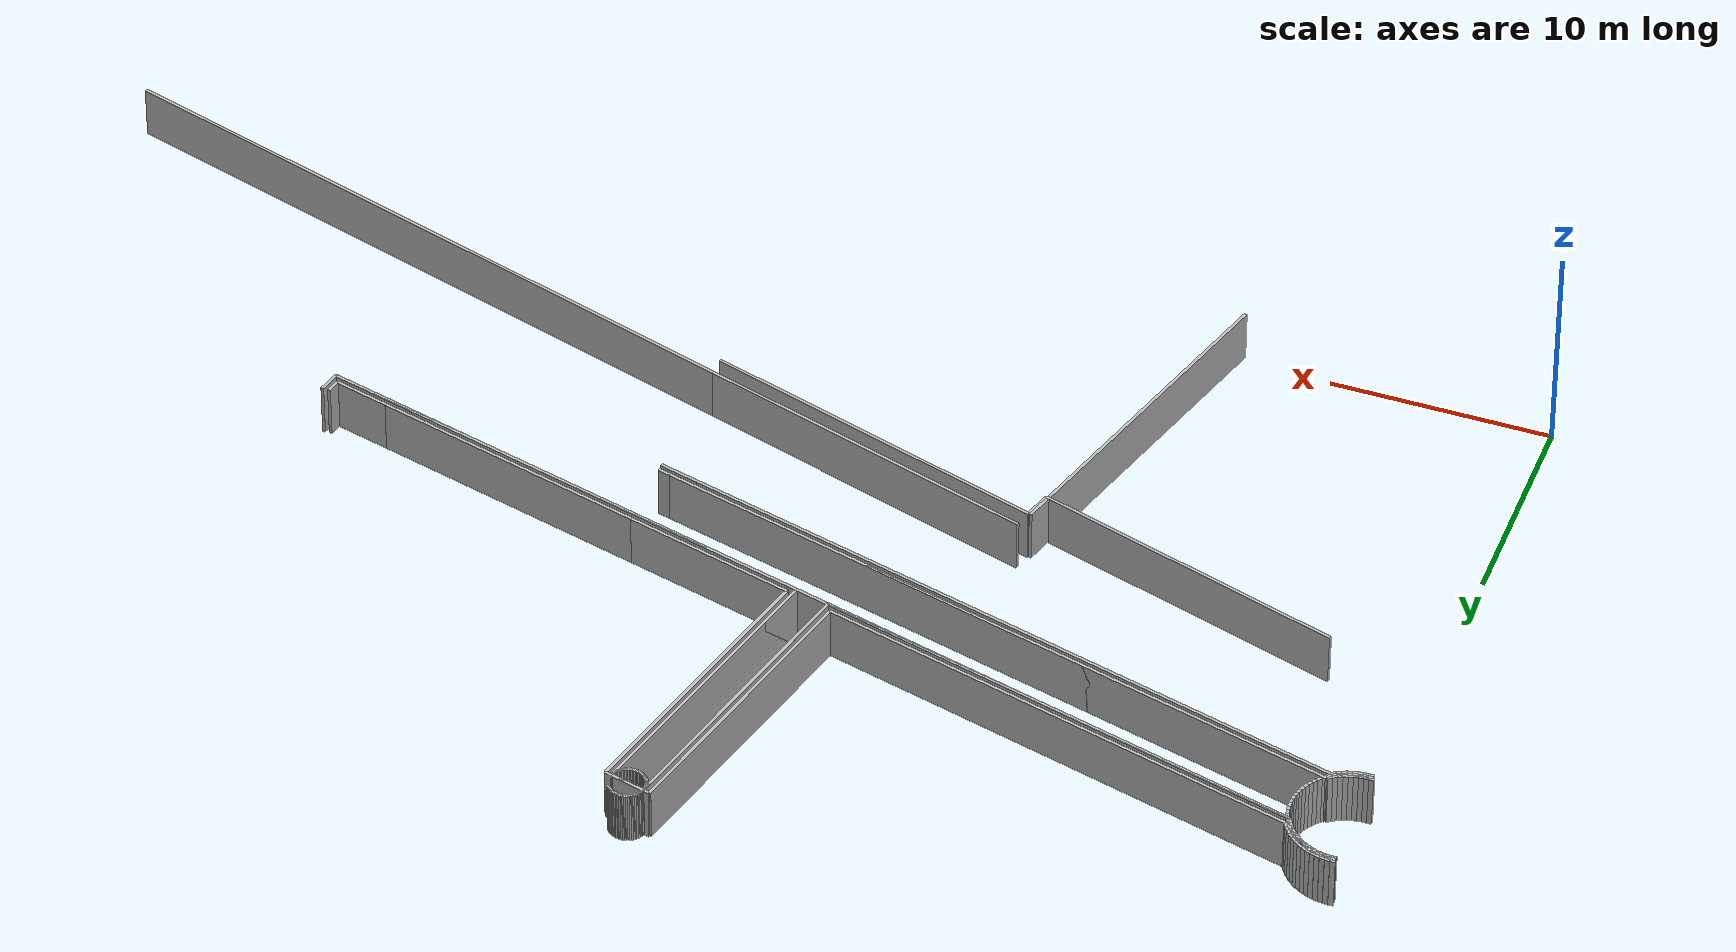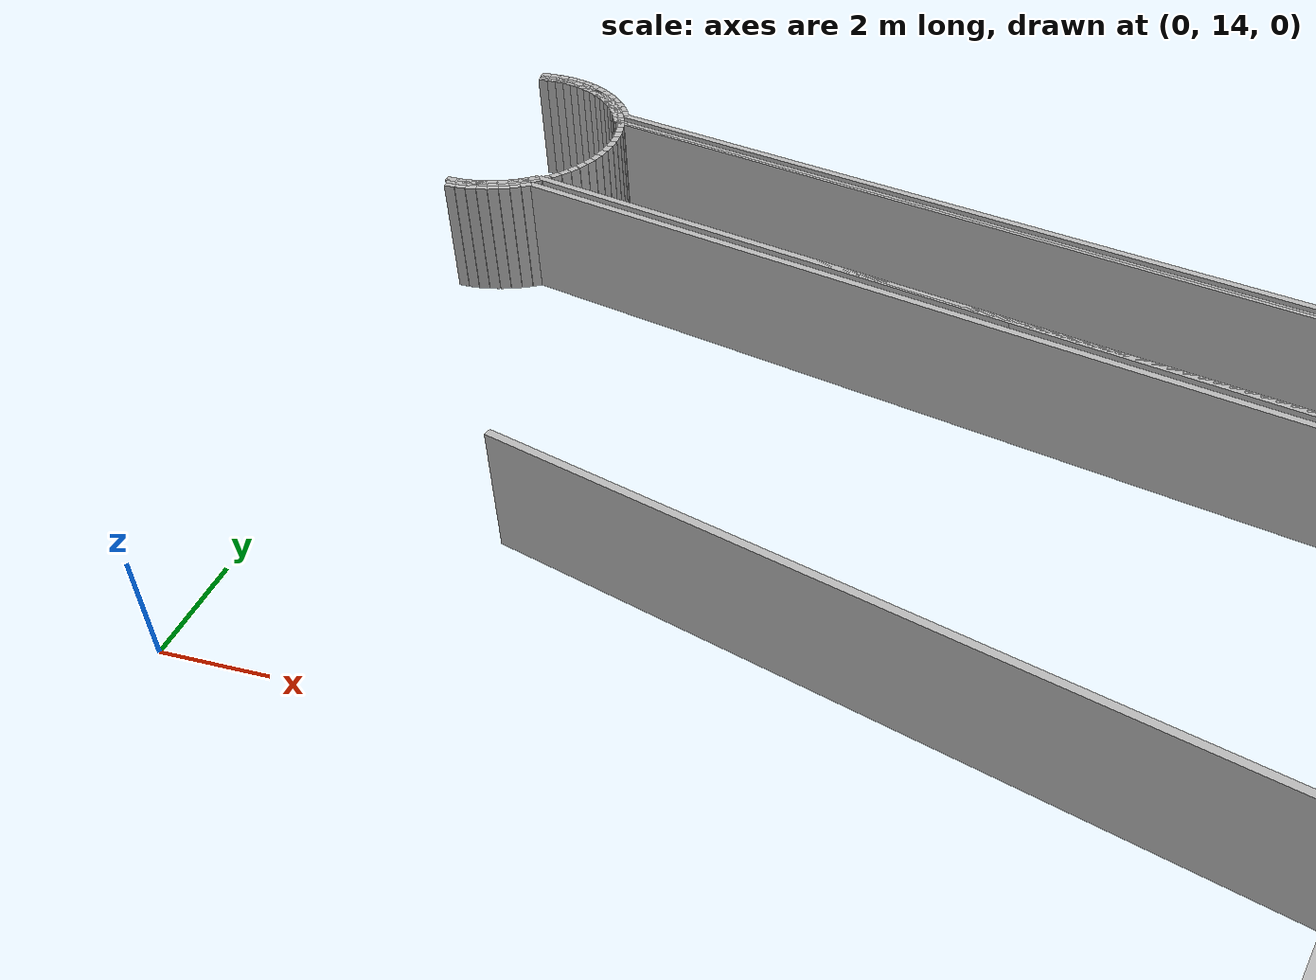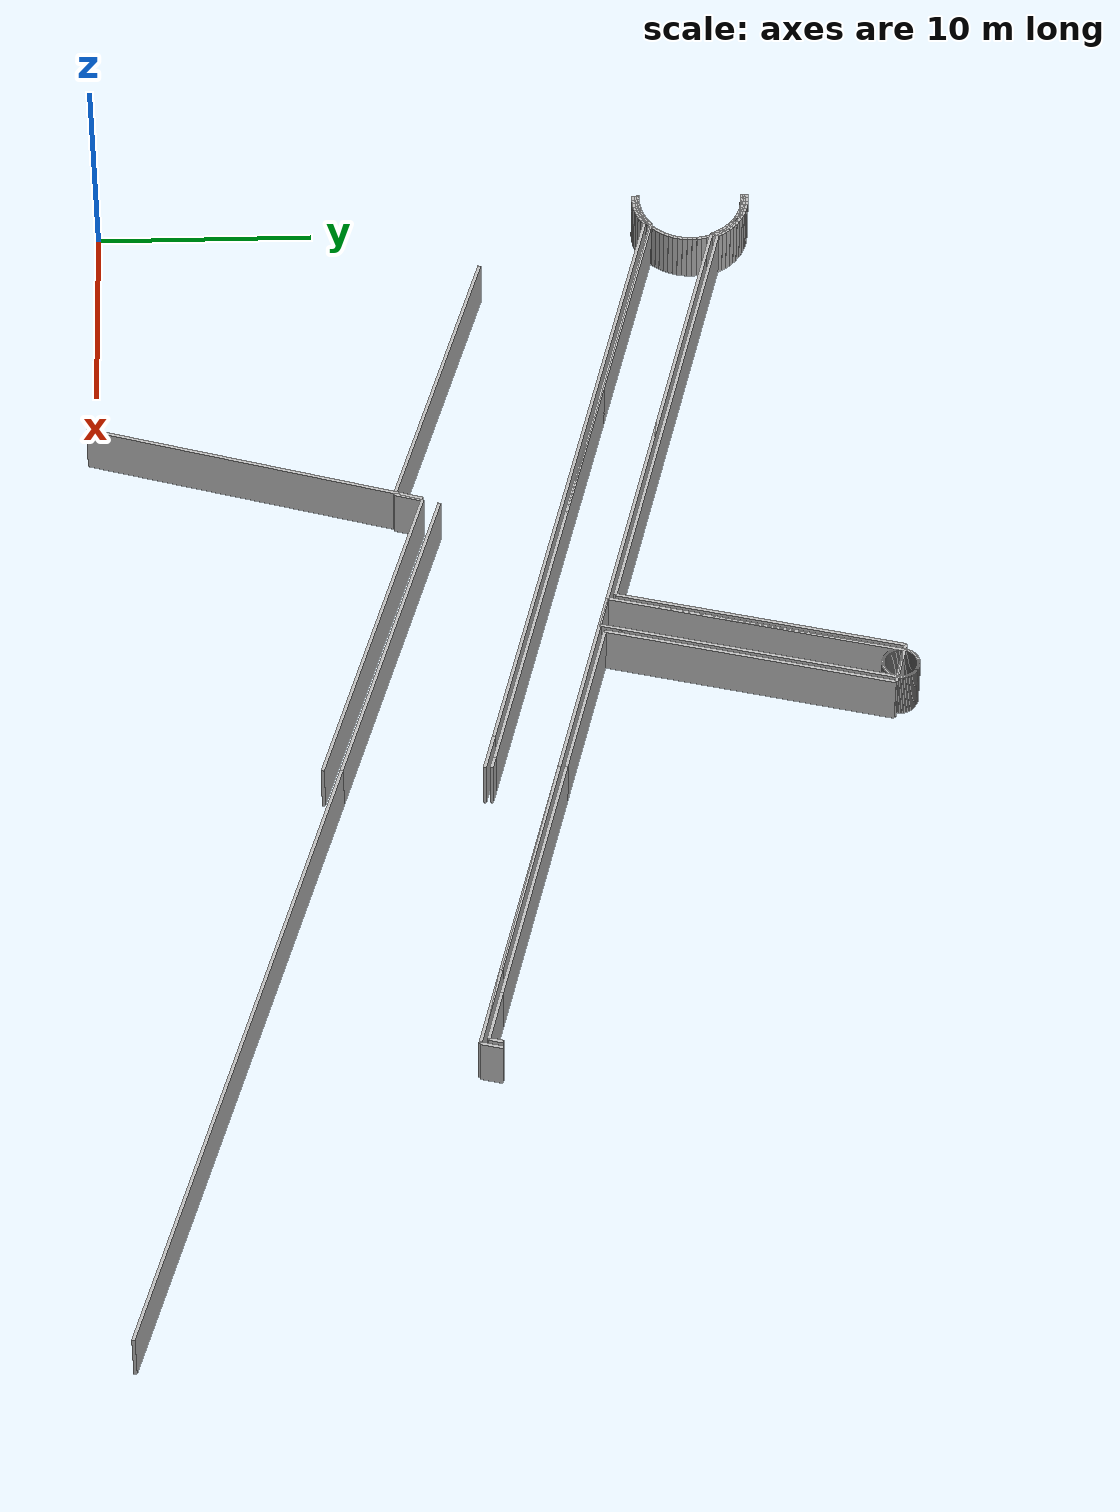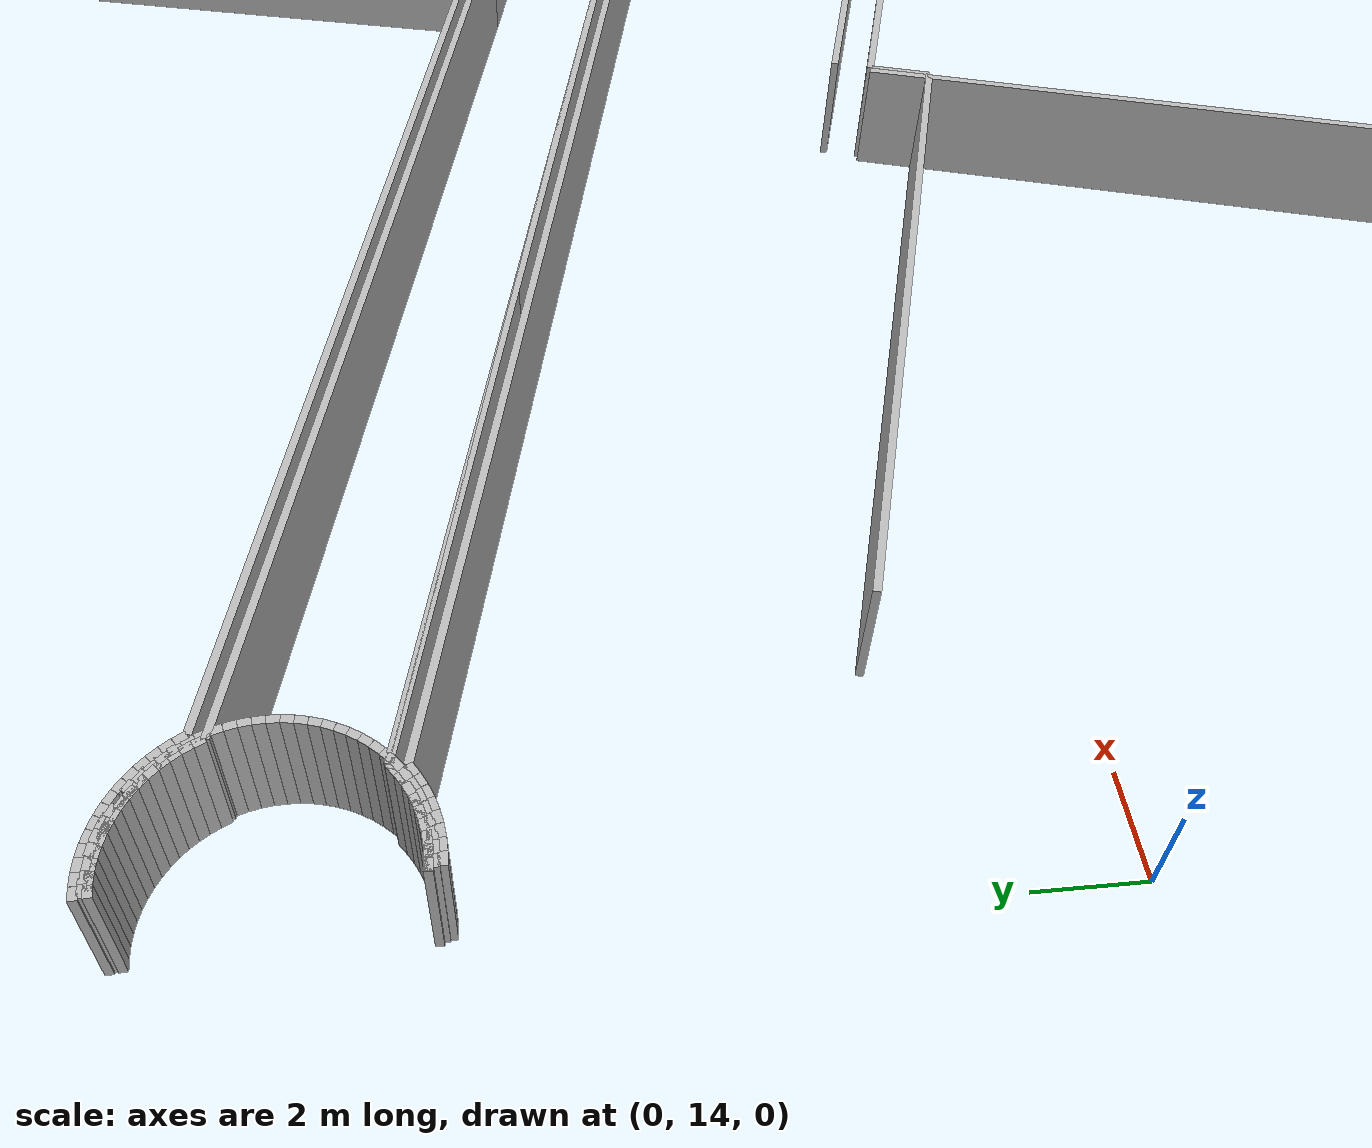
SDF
<?xml version="1.0" ?>
<sdf version="1.6">
  <model name="sps_0108">
    <pose frame="">0 0 0 0 -0 0</pose>
    <static>1</static>
    <self_collide>0</self_collide>
    <allow_auto_disable>0</allow_auto_disable>
    <link name="Wall15">
      <kinematic>0</kinematic>
      <gravity>1</gravity>
      <self_collide>0</self_collide>
      <collision name="collision">
        <geometry>
          <box>
            <size>22.9368 0.15 2.5</size>
          </box>
        </geometry>
        <pose frame="">0 0 0 0 -0 0</pose>
      </collision>
      <visual name="visual">
        <geometry>
          <box>
            <size>22.9368 0.15 2.5</size>
          </box>
        </geometry>
        <pose frame="">0 0 0 0 -0 0</pose>
        <cast_shadows>1</cast_shadows>
        <transparency>0.0</transparency>
      </visual>
      <pose frame="">13.6903 25.9987 1.25 0 -0 2.8938</pose>
    </link>
    <link name="Wall16">
      <kinematic>0</kinematic>
      <gravity>1</gravity>
      <self_collide>0</self_collide>
      <collision name="collision">
        <geometry>
          <box>
            <size>13.5896 0.15 2.5</size>
          </box>
        </geometry>
        <pose frame="">0 0 0 0 -0 0</pose>
      </collision>
      <visual name="visual">
        <geometry>
          <box>
            <size>13.5896 0.15 2.5</size>
          </box>
        </geometry>
        <pose frame="">0 0 0 0 -0 0</pose>
        <cast_shadows>1</cast_shadows>
        <transparency>0.0</transparency>
      </visual>
      <pose frame="">28.0263 29.3809 1.25 0 0 -1.81851</pose>
    </link>
    <link name="Wall17">
      <kinematic>0</kinematic>
      <gravity>1</gravity>
      <self_collide>0</self_collide>
      <collision name="collision">
        <geometry>
          <box>
            <size>2.20059 0.15 2.5</size>
          </box>
        </geometry>
        <pose frame="">0 0 0 0 -0 0</pose>
      </collision>
      <visual name="visual">
        <geometry>
          <box>
            <size>2.20059 0.15 2.5</size>
          </box>
        </geometry>
        <pose frame="">0 0 0 0 -0 0</pose>
        <cast_shadows>1</cast_shadows>
        <transparency>0.0</transparency>
      </visual>
      <pose frame="">28.9172 36.1646 1.25 0 0 -0.247824</pose>
    </link>
    <link name="Wall397">
      <kinematic>0</kinematic>
      <gravity>1</gravity>
      <self_collide>0</self_collide>
      <collision name="collision">
        <geometry>
          <box>
            <size>2.55983 0.15 2.5</size>
          </box>
        </geometry>
        <pose frame="">0 0 0 0 -0 0</pose>
      </collision>
      <visual name="visual">
        <geometry>
          <box>
            <size>2.55983 0.15 2.5</size>
          </box>
        </geometry>
        <pose frame="">0 0 0 0 -0 0</pose>
        <cast_shadows>1</cast_shadows>
        <transparency>0.0</transparency>
      </visual>
      <pose frame="">48.1957 17.5792 1.25 0 -0 2.89381</pose>
    </link>
    <link name="Wall398">
      <kinematic>0</kinematic>
      <gravity>1</gravity>
      <self_collide>0</self_collide>
      <collision name="collision">
        <geometry>
          <box>
            <size>12.8787 0.15 2.5</size>
          </box>
        </geometry>
        <pose frame="">0 0 0 0 -0 0</pose>
      </collision>
      <visual name="visual">
        <geometry>
          <box>
            <size>12.8787 0.15 2.5</size>
          </box>
        </geometry>
        <pose frame="">0 0 0 0 -0 0</pose>
        <cast_shadows>1</cast_shadows>
        <transparency>0.0</transparency>
      </visual>
      <pose frame="">40.7121 19.4724 1.25 0 -0 2.89381</pose>
    </link>
    <link name="Wall399">
      <kinematic>0</kinematic>
      <gravity>1</gravity>
      <self_collide>0</self_collide>
      <collision name="collision">
        <geometry>
          <box>
            <size>7.98962 0.15 2.5</size>
          </box>
        </geometry>
        <pose frame="">0 0 0 0 -0 0</pose>
      </collision>
      <visual name="visual">
        <geometry>
          <box>
            <size>7.98962 0.15 2.5</size>
          </box>
        </geometry>
        <pose frame="">0 0 0 0 -0 0</pose>
        <cast_shadows>1</cast_shadows>
        <transparency>0.0</transparency>
      </visual>
      <pose frame="">30.5966 22.0314 1.25 0 -0 2.89381</pose>
    </link>
    <link name="Wall447">
      <kinematic>0</kinematic>
      <gravity>1</gravity>
      <self_collide>0</self_collide>
      <collision name="collision">
        <geometry>
          <box>
            <size>0.578915 0.15 2.5</size>
          </box>
        </geometry>
        <pose frame="">0 0 0 0 -0 0</pose>
      </collision>
      <visual name="visual">
        <geometry>
          <box>
            <size>0.578915 0.15 2.5</size>
          </box>
        </geometry>
        <pose frame="">0 0 0 0 -0 0</pose>
        <cast_shadows>1</cast_shadows>
        <transparency>0.0</transparency>
      </visual>
      <pose frame="">34.1888 17.8221 1.25 0 -0 2.89383</pose>
    </link>
    <link name="Wall448">
      <kinematic>0</kinematic>
      <gravity>1</gravity>
      <self_collide>0</self_collide>
      <collision name="collision">
        <geometry>
          <box>
            <size>33.0564 0.15 2.5</size>
          </box>
        </geometry>
        <pose frame="">0 0 0 0 -0 0</pose>
      </collision>
      <visual name="visual">
        <geometry>
          <box>
            <size>33.0564 0.15 2.5</size>
          </box>
        </geometry>
        <pose frame="">0 0 0 0 -0 0</pose>
        <cast_shadows>1</cast_shadows>
        <transparency>0.0</transparency>
      </visual>
      <pose frame="">17.8847 21.9464 1.25 0 -0 2.89383</pose>
    </link>
    <link name="Wall737">
      <kinematic>0</kinematic>
      <gravity>1</gravity>
      <self_collide>0</self_collide>
      <collision name="collision">
        <geometry>
          <box>
            <size>1.30961 0.15 2.5</size>
          </box>
        </geometry>
        <pose frame="">0 0 0 0 -0 0</pose>
      </collision>
      <visual name="visual">
        <geometry>
          <box>
            <size>1.30961 0.15 2.5</size>
          </box>
        </geometry>
        <pose frame="">0 0 0 0 -0 0</pose>
        <cast_shadows>1</cast_shadows>
        <transparency>0.0</transparency>
      </visual>
      <pose frame="">18.5507 14.3491 1.25 0 -0 1.28695</pose>
    </link>
    <link name="Wall741">
      <kinematic>0</kinematic>
      <gravity>1</gravity>
      <self_collide>0</self_collide>
      <collision name="collision">
        <geometry>
          <box>
            <size>1.60048 0.15 2.5</size>
          </box>
        </geometry>
        <pose frame="">0 0 0 0 -0 0</pose>
      </collision>
      <visual name="visual">
        <geometry>
          <box>
            <size>1.60048 0.15 2.5</size>
          </box>
        </geometry>
        <pose frame="">0 0 0 0 -0 0</pose>
        <cast_shadows>1</cast_shadows>
        <transparency>0.0</transparency>
      </visual>
      <pose frame="">25.5845 22.9898 1.25 0 -0 2.89374</pose>
    </link>
    <link name="Wall742">
      <kinematic>0</kinematic>
      <gravity>1</gravity>
      <self_collide>0</self_collide>
      <collision name="collision">
        <geometry>
          <box>
            <size>1.59923 0.15 2.5</size>
          </box>
        </geometry>
        <pose frame="">0 0 0 0 -0 0</pose>
      </collision>
      <visual name="visual">
        <geometry>
          <box>
            <size>1.59923 0.15 2.5</size>
          </box>
        </geometry>
        <pose frame="">0 0 0 0 -0 0</pose>
        <cast_shadows>1</cast_shadows>
        <transparency>0.0</transparency>
      </visual>
      <pose frame="">28.9172 36.1647 1.25 0 0 -0.248172</pose>
    </link>
    <link name="Wall749">
      <kinematic>0</kinematic>
      <gravity>1</gravity>
      <self_collide>0</self_collide>
      <collision name="collision">
        <geometry>
          <box>
            <size>4.0463 0.15 2.5</size>
          </box>
        </geometry>
        <pose frame="">0 0 0 0 -0 0</pose>
      </collision>
      <visual name="visual">
        <geometry>
          <box>
            <size>4.0463 0.15 2.5</size>
          </box>
        </geometry>
        <pose frame="">0 0 0 0 -0 0</pose>
        <cast_shadows>1</cast_shadows>
        <transparency>0.0</transparency>
      </visual>
      <pose frame="">47.6923 17.3969 1.25 0 -0 2.89381</pose>
    </link>
    <link name="Wall750">
      <kinematic>0</kinematic>
      <gravity>1</gravity>
      <self_collide>0</self_collide>
      <collision name="collision">
        <geometry>
          <box>
            <size>11.6163 0.15 2.5</size>
          </box>
        </geometry>
        <pose frame="">0 0 0 0 -0 0</pose>
      </collision>
      <visual name="visual">
        <geometry>
          <box>
            <size>11.6163 0.15 2.5</size>
          </box>
        </geometry>
        <pose frame="">0 0 0 0 -0 0</pose>
        <cast_shadows>1</cast_shadows>
        <transparency>0.0</transparency>
      </visual>
      <pose frame="">40.1002 19.3175 1.25 0 -0 2.89381</pose>
    </link>
    <link name="Wall751">
      <kinematic>0</kinematic>
      <gravity>1</gravity>
      <self_collide>0</self_collide>
      <collision name="collision">
        <geometry>
          <box>
            <size>8.36466 0.15 2.5</size>
          </box>
        </geometry>
        <pose frame="">0 0 0 0 -0 0</pose>
      </collision>
      <visual name="visual">
        <geometry>
          <box>
            <size>8.36466 0.15 2.5</size>
          </box>
        </geometry>
        <pose frame="">0 0 0 0 -0 0</pose>
        <cast_shadows>1</cast_shadows>
        <transparency>0.0</transparency>
      </visual>
      <pose frame="">30.4148 21.7677 1.25 0 -0 2.89381</pose>
    </link>
    <link name="Wall787">
      <kinematic>0</kinematic>
      <gravity>1</gravity>
      <self_collide>0</self_collide>
      <collision name="collision">
        <geometry>
          <box>
            <size>31.8407 0.15 2.5</size>
          </box>
        </geometry>
        <pose frame="">0 0 0 0 -0 0</pose>
      </collision>
      <visual name="visual">
        <geometry>
          <box>
            <size>31.8407 0.15 2.5</size>
          </box>
        </geometry>
        <pose frame="">0 0 0 0 -0 0</pose>
        <cast_shadows>1</cast_shadows>
        <transparency>0.0</transparency>
      </visual>
      <pose frame="">17.2501 21.7974 1.25 0 0 -0.247766</pose>
    </link>
    <link name="Wall788">
      <kinematic>0</kinematic>
      <gravity>1</gravity>
      <self_collide>0</self_collide>
      <collision name="collision">
        <geometry>
          <box>
            <size>1.84141 0.15 2.5</size>
          </box>
        </geometry>
        <pose frame="">0 0 0 0 -0 0</pose>
      </collision>
      <visual name="visual">
        <geometry>
          <box>
            <size>1.84141 0.15 2.5</size>
          </box>
        </geometry>
        <pose frame="">0 0 0 0 -0 0</pose>
        <cast_shadows>1</cast_shadows>
        <transparency>0.0</transparency>
      </visual>
      <pose frame="">33.5769 17.6673 1.25 0 0 -0.247766</pose>
    </link>
    <link name="Wall1126">
      <kinematic>0</kinematic>
      <gravity>1</gravity>
      <self_collide>0</self_collide>
      <collision name="collision">
        <geometry>
          <box>
            <size>22.6074 0.15 2.5</size>
          </box>
        </geometry>
        <pose frame="">0 0 0 0 -0 0</pose>
      </collision>
      <visual name="visual">
        <geometry>
          <box>
            <size>22.6074 0.15 2.5</size>
          </box>
        </geometry>
        <pose frame="">0 0 0 0 -0 0</pose>
        <cast_shadows>1</cast_shadows>
        <transparency>0.0</transparency>
      </visual>
      <pose frame="">13.633 26.3228 1.25 0 -0 2.89379</pose>
    </link>
    <link name="Wall1127">
      <kinematic>0</kinematic>
      <gravity>1</gravity>
      <self_collide>0</self_collide>
      <collision name="collision">
        <geometry>
          <box>
            <size>13.2899 0.15 2.5</size>
          </box>
        </geometry>
        <pose frame="">0 0 0 0 -0 0</pose>
      </collision>
      <visual name="visual">
        <geometry>
          <box>
            <size>13.2899 0.15 2.5</size>
          </box>
        </geometry>
        <pose frame="">0 0 0 0 -0 0</pose>
        <cast_shadows>1</cast_shadows>
        <transparency>0.0</transparency>
      </visual>
      <pose frame="">26.221 29.9924 1.25 0 0 -1.81855</pose>
    </link>
    <link name="Wall1152">
      <kinematic>0</kinematic>
      <gravity>1</gravity>
      <self_collide>0</self_collide>
      <collision name="collision">
        <geometry>
          <box>
            <size>16.1848 0.15 2.5</size>
          </box>
        </geometry>
        <pose frame="">0 0 0 0 -0 0</pose>
      </collision>
      <visual name="visual">
        <geometry>
          <box>
            <size>16.1848 0.15 2.5</size>
          </box>
        </geometry>
        <pose frame="">0 0 0 0 -0 0</pose>
        <cast_shadows>1</cast_shadows>
        <transparency>0.0</transparency>
      </visual>
      <pose frame="">26.7132 13.4373 1.25 0 0 -0.289268</pose>
    </link>
    <link name="Wall1153">
      <kinematic>0</kinematic>
      <gravity>1</gravity>
      <self_collide>0</self_collide>
      <collision name="collision">
        <geometry>
          <box>
            <size>31.5682 0.15 2.5</size>
          </box>
        </geometry>
        <pose frame="">0 0 0 0 -0 0</pose>
      </collision>
      <visual name="visual">
        <geometry>
          <box>
            <size>31.5682 0.15 2.5</size>
          </box>
        </geometry>
        <pose frame="">0 0 0 0 -0 0</pose>
        <cast_shadows>1</cast_shadows>
        <transparency>0.0</transparency>
      </visual>
      <pose frame="">49.5977 6.62652 1.25 0 0 -0.289268</pose>
    </link>
    <link name="Wall1454">
      <kinematic>0</kinematic>
      <gravity>1</gravity>
      <self_collide>0</self_collide>
      <collision name="collision">
        <geometry>
          <box>
            <size>14.6296 0.15 2.5</size>
          </box>
        </geometry>
        <pose frame="">0 0 0 0 -0 0</pose>
      </collision>
      <visual name="visual">
        <geometry>
          <box>
            <size>14.6296 0.15 2.5</size>
          </box>
        </geometry>
        <pose frame="">0 0 0 0 -0 0</pose>
        <cast_shadows>1</cast_shadows>
        <transparency>0.0</transparency>
      </visual>
      <pose frame="">11.3563 15.8068 1.25 0 0 -0.289232</pose>
    </link>
    <link name="Wall1458">
      <kinematic>0</kinematic>
      <gravity>1</gravity>
      <self_collide>0</self_collide>
      <collision name="collision">
        <geometry>
          <box>
            <size>13.5904 0.15 2.5</size>
          </box>
        </geometry>
        <pose frame="">0 0 0 0 -0 0</pose>
      </collision>
      <visual name="visual">
        <geometry>
          <box>
            <size>13.5904 0.15 2.5</size>
          </box>
        </geometry>
        <pose frame="">0 0 0 0 -0 0</pose>
        <cast_shadows>1</cast_shadows>
        <transparency>0.0</transparency>
      </visual>
      <pose frame="">26.4752 29.7735 1.25 0 -0 1.32298</pose>
    </link>
    <link name="Wall1760">
      <kinematic>0</kinematic>
      <gravity>1</gravity>
      <self_collide>0</self_collide>
      <collision name="collision">
        <geometry>
          <box>
            <size>1.02361 0.15 2.5</size>
          </box>
        </geometry>
        <pose frame="">0 0 0 0 -0 0</pose>
      </collision>
      <visual name="visual">
        <geometry>
          <box>
            <size>1.02361 0.15 2.5</size>
          </box>
        </geometry>
        <pose frame="">0 0 0 0 -0 0</pose>
        <cast_shadows>1</cast_shadows>
        <transparency>0.0</transparency>
      </visual>
      <pose frame="">49.7791 17.3969 1.25 0 -0 1.32309</pose>
    </link>
    <link name="Wall2087">
      <kinematic>0</kinematic>
      <gravity>1</gravity>
      <self_collide>0</self_collide>
      <collision name="collision">
        <geometry>
          <box>
            <size>13.2896 0.15 2.5</size>
          </box>
        </geometry>
        <pose frame="">0 0 0 0 -0 0</pose>
      </collision>
      <visual name="visual">
        <geometry>
          <box>
            <size>13.2896 0.15 2.5</size>
          </box>
        </geometry>
        <pose frame="">0 0 0 0 -0 0</pose>
        <cast_shadows>1</cast_shadows>
        <transparency>0.0</transparency>
      </visual>
      <pose frame="">28.3538 29.4529 1.25 0 -0 1.32296</pose>
    </link>
    <link name="Wall2476">
      <kinematic>0</kinematic>
      <gravity>1</gravity>
      <self_collide>0</self_collide>
      <collision name="collision">
        <geometry>
          <box>
            <size>0.647582 0.15 2.5</size>
          </box>
        </geometry>
        <pose frame="">0 0 0 0 -0 0</pose>
      </collision>
      <visual name="visual">
        <geometry>
          <box>
            <size>0.647582 0.15 2.5</size>
          </box>
        </geometry>
        <pose frame="">0 0 0 0 -0 0</pose>
        <cast_shadows>1</cast_shadows>
        <transparency>0.0</transparency>
      </visual>
      <pose frame="">49.5159 17.5792 1.25 0 0 -1.81855</pose>
    </link>
    <link name="Wall2521">
      <kinematic>0</kinematic>
      <gravity>1</gravity>
      <self_collide>0</self_collide>
      <collision name="collision">
        <geometry>
          <box>
            <size>16.4184 0.15 2.5</size>
          </box>
        </geometry>
        <pose frame="">0 0 0 0 -0 0</pose>
      </collision>
      <visual name="visual">
        <geometry>
          <box>
            <size>16.4184 0.15 2.5</size>
          </box>
        </geometry>
        <pose frame="">0 0 0 0 -0 0</pose>
        <cast_shadows>1</cast_shadows>
        <transparency>0.0</transparency>
      </visual>
      <pose frame="">26.6017 12.6346 1.25 0 0 -0.289445</pose>
    </link>
    <link name="Wall3677">
      <kinematic>0</kinematic>
      <gravity>1</gravity>
      <self_collide>0</self_collide>
      <collision name="collision">
        <geometry>
          <box>
            <size>0.222353 0.15 2.5</size>
          </box>
        </geometry>
        <pose frame="">0 0 0 0 -0 0</pose>
      </collision>
      <visual name="visual">
        <geometry>
          <box>
            <size>0.222353 0.15 2.5</size>
          </box>
        </geometry>
        <pose frame="">0 0 0 0 -0 0</pose>
        <cast_shadows>1</cast_shadows>
        <transparency>0.0</transparency>
      </visual>
      <pose frame="">1.83828 29.9144 1.25 0 0 -0.654591</pose>
    </link>
    <link name="Wall3678">
      <kinematic>0</kinematic>
      <gravity>1</gravity>
      <self_collide>0</self_collide>
      <collision name="collision">
        <geometry>
          <box>
            <size>0.222517 0.15 2.5</size>
          </box>
        </geometry>
        <pose frame="">0 0 0 0 -0 0</pose>
      </collision>
      <visual name="visual">
        <geometry>
          <box>
            <size>0.222517 0.15 2.5</size>
          </box>
        </geometry>
        <pose frame="">0 0 0 0 -0 0</pose>
        <cast_shadows>1</cast_shadows>
        <transparency>0.0</transparency>
      </visual>
      <pose frame="">2.00848 29.7715 1.25 0 0 -0.742133</pose>
    </link>
    <link name="Wall3679">
      <kinematic>0</kinematic>
      <gravity>1</gravity>
      <self_collide>0</self_collide>
      <collision name="collision">
        <geometry>
          <box>
            <size>0.222393 0.15 2.5</size>
          </box>
        </geometry>
        <pose frame="">0 0 0 0 -0 0</pose>
      </collision>
      <visual name="visual">
        <geometry>
          <box>
            <size>0.222393 0.15 2.5</size>
          </box>
        </geometry>
        <pose frame="">0 0 0 0 -0 0</pose>
        <cast_shadows>1</cast_shadows>
        <transparency>0.0</transparency>
      </visual>
      <pose frame="">2.16558 29.6143 1.25 0 0 -0.829271</pose>
    </link>
    <link name="Wall3680">
      <kinematic>0</kinematic>
      <gravity>1</gravity>
      <self_collide>0</self_collide>
      <collision name="collision">
        <geometry>
          <box>
            <size>0.222546 0.15 2.5</size>
          </box>
        </geometry>
        <pose frame="">0 0 0 0 -0 0</pose>
      </collision>
      <visual name="visual">
        <geometry>
          <box>
            <size>0.222546 0.15 2.5</size>
          </box>
        </geometry>
        <pose frame="">0 0 0 0 -0 0</pose>
        <cast_shadows>1</cast_shadows>
        <transparency>0.0</transparency>
      </visual>
      <pose frame="">2.30837 29.444 1.25 0 0 -0.916873</pose>
    </link>
    <link name="Wall3681">
      <kinematic>0</kinematic>
      <gravity>1</gravity>
      <self_collide>0</self_collide>
      <collision name="collision">
        <geometry>
          <box>
            <size>0.222333 0.15 2.5</size>
          </box>
        </geometry>
        <pose frame="">0 0 0 0 -0 0</pose>
      </collision>
      <visual name="visual">
        <geometry>
          <box>
            <size>0.222333 0.15 2.5</size>
          </box>
        </geometry>
        <pose frame="">0 0 0 0 -0 0</pose>
        <cast_shadows>1</cast_shadows>
        <transparency>0.0</transparency>
      </visual>
      <pose frame="">2.43575 29.2619 1.25 0 0 -1.00396</pose>
    </link>
    <link name="Wall3682">
      <kinematic>0</kinematic>
      <gravity>1</gravity>
      <self_collide>0</self_collide>
      <collision name="collision">
        <geometry>
          <box>
            <size>0.222461 0.15 2.5</size>
          </box>
        </geometry>
        <pose frame="">0 0 0 0 -0 0</pose>
      </collision>
      <visual name="visual">
        <geometry>
          <box>
            <size>0.222461 0.15 2.5</size>
          </box>
        </geometry>
        <pose frame="">0 0 0 0 -0 0</pose>
        <cast_shadows>1</cast_shadows>
        <transparency>0.0</transparency>
      </visual>
      <pose frame="">2.54674 29.0694 1.25 0 0 -1.09144</pose>
    </link>
    <link name="Wall3683">
      <kinematic>0</kinematic>
      <gravity>1</gravity>
      <self_collide>0</self_collide>
      <collision name="collision">
        <geometry>
          <box>
            <size>0.222582 0.15 2.5</size>
          </box>
        </geometry>
        <pose frame="">0 0 0 0 -0 0</pose>
      </collision>
      <visual name="visual">
        <geometry>
          <box>
            <size>0.222582 0.15 2.5</size>
          </box>
        </geometry>
        <pose frame="">0 0 0 0 -0 0</pose>
        <cast_shadows>1</cast_shadows>
        <transparency>0.0</transparency>
      </visual>
      <pose frame="">2.64065 28.8679 1.25 0 0 -1.17797</pose>
    </link>
    <link name="Wall3684">
      <kinematic>0</kinematic>
      <gravity>1</gravity>
      <self_collide>0</self_collide>
      <collision name="collision">
        <geometry>
          <box>
            <size>0.222494 0.15 2.5</size>
          </box>
        </geometry>
        <pose frame="">0 0 0 0 -0 0</pose>
      </collision>
      <visual name="visual">
        <geometry>
          <box>
            <size>0.222494 0.15 2.5</size>
          </box>
        </geometry>
        <pose frame="">0 0 0 0 -0 0</pose>
        <cast_shadows>1</cast_shadows>
        <transparency>0.0</transparency>
      </visual>
      <pose frame="">2.71667 28.659 1.25 0 0 -1.2657</pose>
    </link>
    <link name="Wall3685">
      <kinematic>0</kinematic>
      <gravity>1</gravity>
      <self_collide>0</self_collide>
      <collision name="collision">
        <geometry>
          <box>
            <size>0.222438 0.15 2.5</size>
          </box>
        </geometry>
        <pose frame="">0 0 0 0 -0 0</pose>
      </collision>
      <visual name="visual">
        <geometry>
          <box>
            <size>0.222438 0.15 2.5</size>
          </box>
        </geometry>
        <pose frame="">0 0 0 0 -0 0</pose>
        <cast_shadows>1</cast_shadows>
        <transparency>0.0</transparency>
      </visual>
      <pose frame="">2.77416 28.4443 1.25 0 0 -1.35257</pose>
    </link>
    <link name="Wall3686">
      <kinematic>0</kinematic>
      <gravity>1</gravity>
      <self_collide>0</self_collide>
      <collision name="collision">
        <geometry>
          <box>
            <size>0.222515 0.15 2.5</size>
          </box>
        </geometry>
        <pose frame="">0 0 0 0 -0 0</pose>
      </collision>
      <visual name="visual">
        <geometry>
          <box>
            <size>0.222515 0.15 2.5</size>
          </box>
        </geometry>
        <pose frame="">0 0 0 0 -0 0</pose>
        <cast_shadows>1</cast_shadows>
        <transparency>0.0</transparency>
      </visual>
      <pose frame="">2.81264 28.2254 1.25 0 0 -1.44096</pose>
    </link>
    <link name="Wall3687">
      <kinematic>0</kinematic>
      <gravity>1</gravity>
      <self_collide>0</self_collide>
      <collision name="collision">
        <geometry>
          <box>
            <size>0.222375 0.15 2.5</size>
          </box>
        </geometry>
        <pose frame="">0 0 0 0 -0 0</pose>
      </collision>
      <visual name="visual">
        <geometry>
          <box>
            <size>0.222375 0.15 2.5</size>
          </box>
        </geometry>
        <pose frame="">0 0 0 0 -0 0</pose>
        <cast_shadows>1</cast_shadows>
        <transparency>0.0</transparency>
      </visual>
      <pose frame="">2.83184 28.004 1.25 0 0 -1.52769</pose>
    </link>
    <link name="Wall3688">
      <kinematic>0</kinematic>
      <gravity>1</gravity>
      <self_collide>0</self_collide>
      <collision name="collision">
        <geometry>
          <box>
            <size>0.222436 0.15 2.5</size>
          </box>
        </geometry>
        <pose frame="">0 0 0 0 -0 0</pose>
      </collision>
      <visual name="visual">
        <geometry>
          <box>
            <size>0.222436 0.15 2.5</size>
          </box>
        </geometry>
        <pose frame="">0 0 0 0 -0 0</pose>
        <cast_shadows>1</cast_shadows>
        <transparency>0.0</transparency>
      </visual>
      <pose frame="">2.83184 27.7818 1.25 0 0 -1.61389</pose>
    </link>
    <link name="Wall3689">
      <kinematic>0</kinematic>
      <gravity>1</gravity>
      <self_collide>0</self_collide>
      <collision name="collision">
        <geometry>
          <box>
            <size>0.222502 0.15 2.5</size>
          </box>
        </geometry>
        <pose frame="">0 0 0 0 -0 0</pose>
      </collision>
      <visual name="visual">
        <geometry>
          <box>
            <size>0.222502 0.15 2.5</size>
          </box>
        </geometry>
        <pose frame="">0 0 0 0 -0 0</pose>
        <cast_shadows>1</cast_shadows>
        <transparency>0.0</transparency>
      </visual>
      <pose frame="">2.81246 27.5604 1.25 0 0 -1.7023</pose>
    </link>
    <link name="Wall3690">
      <kinematic>0</kinematic>
      <gravity>1</gravity>
      <self_collide>0</self_collide>
      <collision name="collision">
        <geometry>
          <box>
            <size>0.222511 0.15 2.5</size>
          </box>
        </geometry>
        <pose frame="">0 0 0 0 -0 0</pose>
      </collision>
      <visual name="visual">
        <geometry>
          <box>
            <size>0.222511 0.15 2.5</size>
          </box>
        </geometry>
        <pose frame="">0 0 0 0 -0 0</pose>
        <cast_shadows>1</cast_shadows>
        <transparency>0.0</transparency>
      </visual>
      <pose frame="">2.77376 27.3415 1.25 0 0 -1.78923</pose>
    </link>
    <link name="Wall3691">
      <kinematic>0</kinematic>
      <gravity>1</gravity>
      <self_collide>0</self_collide>
      <collision name="collision">
        <geometry>
          <box>
            <size>0.222317 0.15 2.5</size>
          </box>
        </geometry>
        <pose frame="">0 0 0 0 -0 0</pose>
      </collision>
      <visual name="visual">
        <geometry>
          <box>
            <size>0.222317 0.15 2.5</size>
          </box>
        </geometry>
        <pose frame="">0 0 0 0 -0 0</pose>
        <cast_shadows>1</cast_shadows>
        <transparency>0.0</transparency>
      </visual>
      <pose frame="">2.71615 27.1269 1.25 0 0 -1.87701</pose>
    </link>
    <link name="Wall3692">
      <kinematic>0</kinematic>
      <gravity>1</gravity>
      <self_collide>0</self_collide>
      <collision name="collision">
        <geometry>
          <box>
            <size>0.222525 0.15 2.5</size>
          </box>
        </geometry>
        <pose frame="">0 0 0 0 -0 0</pose>
      </collision>
      <visual name="visual">
        <geometry>
          <box>
            <size>0.222525 0.15 2.5</size>
          </box>
        </geometry>
        <pose frame="">0 0 0 0 -0 0</pose>
        <cast_shadows>1</cast_shadows>
        <transparency>0.0</transparency>
      </visual>
      <pose frame="">2.64004 26.9181 1.25 0 0 -1.96373</pose>
    </link>
    <link name="Wall3693">
      <kinematic>0</kinematic>
      <gravity>1</gravity>
      <self_collide>0</self_collide>
      <collision name="collision">
        <geometry>
          <box>
            <size>0.222298 0.15 2.5</size>
          </box>
        </geometry>
        <pose frame="">0 0 0 0 -0 0</pose>
      </collision>
      <visual name="visual">
        <geometry>
          <box>
            <size>0.222298 0.15 2.5</size>
          </box>
        </geometry>
        <pose frame="">0 0 0 0 -0 0</pose>
        <cast_shadows>1</cast_shadows>
        <transparency>0.0</transparency>
      </visual>
      <pose frame="">2.54613 26.7167 1.25 0 0 -2.05053</pose>
    </link>
    <link name="Wall3694">
      <kinematic>0</kinematic>
      <gravity>1</gravity>
      <self_collide>0</self_collide>
      <collision name="collision">
        <geometry>
          <box>
            <size>0.222483 0.15 2.5</size>
          </box>
        </geometry>
        <pose frame="">0 0 0 0 -0 0</pose>
      </collision>
      <visual name="visual">
        <geometry>
          <box>
            <size>0.222483 0.15 2.5</size>
          </box>
        </geometry>
        <pose frame="">0 0 0 0 -0 0</pose>
        <cast_shadows>1</cast_shadows>
        <transparency>0.0</transparency>
      </visual>
      <pose frame="">2.43505 26.5243 1.25 0 0 -2.13818</pose>
    </link>
    <link name="Wall3695">
      <kinematic>0</kinematic>
      <gravity>1</gravity>
      <self_collide>0</self_collide>
      <collision name="collision">
        <geometry>
          <box>
            <size>0.222501 0.15 2.5</size>
          </box>
        </geometry>
        <pose frame="">0 0 0 0 -0 0</pose>
      </collision>
      <visual name="visual">
        <geometry>
          <box>
            <size>0.222501 0.15 2.5</size>
          </box>
        </geometry>
        <pose frame="">0 0 0 0 -0 0</pose>
        <cast_shadows>1</cast_shadows>
        <transparency>0.0</transparency>
      </visual>
      <pose frame="">2.30746 26.3423 1.25 0 0 -2.22626</pose>
    </link>
    <link name="Wall3696">
      <kinematic>0</kinematic>
      <gravity>1</gravity>
      <self_collide>0</self_collide>
      <collision name="collision">
        <geometry>
          <box>
            <size>0.222393 0.15 2.5</size>
          </box>
        </geometry>
        <pose frame="">0 0 0 0 -0 0</pose>
      </collision>
      <visual name="visual">
        <geometry>
          <box>
            <size>0.222393 0.15 2.5</size>
          </box>
        </geometry>
        <pose frame="">0 0 0 0 -0 0</pose>
        <cast_shadows>1</cast_shadows>
        <transparency>0.0</transparency>
      </visual>
      <pose frame="">2.16454 26.1721 1.25 0 0 -2.31232</pose>
    </link>
    <link name="Wall3697">
      <kinematic>0</kinematic>
      <gravity>1</gravity>
      <self_collide>0</self_collide>
      <collision name="collision">
        <geometry>
          <box>
            <size>0.222528 0.15 2.5</size>
          </box>
        </geometry>
        <pose frame="">0 0 0 0 -0 0</pose>
      </collision>
      <visual name="visual">
        <geometry>
          <box>
            <size>0.222528 0.15 2.5</size>
          </box>
        </geometry>
        <pose frame="">0 0 0 0 -0 0</pose>
        <cast_shadows>1</cast_shadows>
        <transparency>0.0</transparency>
      </visual>
      <pose frame="">2.00735 26.015 1.25 0 0 -2.40062</pose>
    </link>
    <link name="Wall3698">
      <kinematic>0</kinematic>
      <gravity>1</gravity>
      <self_collide>0</self_collide>
      <collision name="collision">
        <geometry>
          <box>
            <size>0.222353 0.15 2.5</size>
          </box>
        </geometry>
        <pose frame="">0 0 0 0 -0 0</pose>
      </collision>
      <visual name="visual">
        <geometry>
          <box>
            <size>0.222353 0.15 2.5</size>
          </box>
        </geometry>
        <pose frame="">0 0 0 0 -0 0</pose>
        <cast_shadows>1</cast_shadows>
        <transparency>0.0</transparency>
      </visual>
      <pose frame="">1.83706 25.8722 1.25 0 0 -2.487</pose>
    </link>
    <link name="Wall3699">
      <kinematic>0</kinematic>
      <gravity>1</gravity>
      <self_collide>0</self_collide>
      <collision name="collision">
        <geometry>
          <box>
            <size>0.22267 0.15 2.5</size>
          </box>
        </geometry>
        <pose frame="">0 0 0 0 -0 0</pose>
      </collision>
      <visual name="visual">
        <geometry>
          <box>
            <size>0.22267 0.15 2.5</size>
          </box>
        </geometry>
        <pose frame="">0 0 0 0 -0 0</pose>
        <cast_shadows>1</cast_shadows>
        <transparency>0.0</transparency>
      </visual>
      <pose frame="">1.65496 25.7447 1.25 0 0 -2.57442</pose>
    </link>
    <link name="Wall3700">
      <kinematic>0</kinematic>
      <gravity>1</gravity>
      <self_collide>0</self_collide>
      <collision name="collision">
        <geometry>
          <box>
            <size>0.222298 0.15 2.5</size>
          </box>
        </geometry>
        <pose frame="">0 0 0 0 -0 0</pose>
      </collision>
      <visual name="visual">
        <geometry>
          <box>
            <size>0.222298 0.15 2.5</size>
          </box>
        </geometry>
        <pose frame="">0 0 0 0 -0 0</pose>
        <cast_shadows>1</cast_shadows>
        <transparency>0.0</transparency>
      </visual>
      <pose frame="">1.46246 25.6336 1.25 0 0 -2.66186</pose>
    </link>
    <link name="Wall3701">
      <kinematic>0</kinematic>
      <gravity>1</gravity>
      <self_collide>0</self_collide>
      <collision name="collision">
        <geometry>
          <box>
            <size>0.222512 0.15 2.5</size>
          </box>
        </geometry>
        <pose frame="">0 0 0 0 -0 0</pose>
      </collision>
      <visual name="visual">
        <geometry>
          <box>
            <size>0.222512 0.15 2.5</size>
          </box>
        </geometry>
        <pose frame="">0 0 0 0 -0 0</pose>
        <cast_shadows>1</cast_shadows>
        <transparency>0.0</transparency>
      </visual>
      <pose frame="">1.26104 25.5398 1.25 0 0 -2.74952</pose>
    </link>
    <link name="Wall3702">
      <kinematic>0</kinematic>
      <gravity>1</gravity>
      <self_collide>0</self_collide>
      <collision name="collision">
        <geometry>
          <box>
            <size>0.222473 0.15 2.5</size>
          </box>
        </geometry>
        <pose frame="">0 0 0 0 -0 0</pose>
      </collision>
      <visual name="visual">
        <geometry>
          <box>
            <size>0.222473 0.15 2.5</size>
          </box>
        </geometry>
        <pose frame="">0 0 0 0 -0 0</pose>
        <cast_shadows>1</cast_shadows>
        <transparency>0.0</transparency>
      </visual>
      <pose frame="">1.05215 25.4638 1.25 0 0 -2.83589</pose>
    </link>
    <link name="Wall3703">
      <kinematic>0</kinematic>
      <gravity>1</gravity>
      <self_collide>0</self_collide>
      <collision name="collision">
        <geometry>
          <box>
            <size>0.222472 0.15 2.5</size>
          </box>
        </geometry>
        <pose frame="">0 0 0 0 -0 0</pose>
      </collision>
      <visual name="visual">
        <geometry>
          <box>
            <size>0.222472 0.15 2.5</size>
          </box>
        </geometry>
        <pose frame="">0 0 0 0 -0 0</pose>
        <cast_shadows>1</cast_shadows>
        <transparency>0.0</transparency>
      </visual>
      <pose frame="">0.837455 25.4063 1.25 0 0 -2.92397</pose>
    </link>
    <link name="Wall3704">
      <kinematic>0</kinematic>
      <gravity>1</gravity>
      <self_collide>0</self_collide>
      <collision name="collision">
        <geometry>
          <box>
            <size>0.222478 0.15 2.5</size>
          </box>
        </geometry>
        <pose frame="">0 0 0 0 -0 0</pose>
      </collision>
      <visual name="visual">
        <geometry>
          <box>
            <size>0.222478 0.15 2.5</size>
          </box>
        </geometry>
        <pose frame="">0 0 0 0 -0 0</pose>
        <cast_shadows>1</cast_shadows>
        <transparency>0.0</transparency>
      </visual>
      <pose frame="">0.618552 25.3678 1.25 0 0 -3.01091</pose>
    </link>
    <link name="Wall3705">
      <kinematic>0</kinematic>
      <gravity>1</gravity>
      <self_collide>0</self_collide>
      <collision name="collision">
        <geometry>
          <box>
            <size>0.222436 0.15 2.5</size>
          </box>
        </geometry>
        <pose frame="">0 0 0 0 -0 0</pose>
      </collision>
      <visual name="visual">
        <geometry>
          <box>
            <size>0.222436 0.15 2.5</size>
          </box>
        </geometry>
        <pose frame="">0 0 0 0 -0 0</pose>
        <cast_shadows>1</cast_shadows>
        <transparency>0.0</transparency>
      </visual>
      <pose frame="">0.397147 25.3485 1.25 0 0 -3.0985</pose>
    </link>
    <link name="Wall3706">
      <kinematic>0</kinematic>
      <gravity>1</gravity>
      <self_collide>0</self_collide>
      <collision name="collision">
        <geometry>
          <box>
            <size>0.222382 0.15 2.5</size>
          </box>
        </geometry>
        <pose frame="">0 0 0 0 -0 0</pose>
      </collision>
      <visual name="visual">
        <geometry>
          <box>
            <size>0.222382 0.15 2.5</size>
          </box>
        </geometry>
        <pose frame="">0 0 0 0 -0 0</pose>
        <cast_shadows>1</cast_shadows>
        <transparency>0.0</transparency>
      </visual>
      <pose frame="">0.174949 25.3486 1.25 0 -0 3.09766</pose>
    </link>
    <link name="Wall3741">
      <kinematic>0</kinematic>
      <gravity>1</gravity>
      <self_collide>0</self_collide>
      <collision name="collision">
        <geometry>
          <box>
            <size>0.222375 0.15 2.5</size>
          </box>
        </geometry>
        <pose frame="">0 0 0 0 -0 0</pose>
      </collision>
      <visual name="visual">
        <geometry>
          <box>
            <size>0.222375 0.15 2.5</size>
          </box>
        </geometry>
        <pose frame="">0 0 0 0 -0 0</pose>
        <cast_shadows>1</cast_shadows>
        <transparency>0.0</transparency>
      </visual>
      <pose frame="">0.176353 30.4389 1.25 0 -0 0.0431052</pose>
    </link>
    <link name="Wall3742">
      <kinematic>0</kinematic>
      <gravity>1</gravity>
      <self_collide>0</self_collide>
      <collision name="collision">
        <geometry>
          <box>
            <size>0.222443 0.15 2.5</size>
          </box>
        </geometry>
        <pose frame="">0 0 0 0 -0 0</pose>
      </collision>
      <visual name="visual">
        <geometry>
          <box>
            <size>0.222443 0.15 2.5</size>
          </box>
        </geometry>
        <pose frame="">0 0 0 0 -0 0</pose>
        <cast_shadows>1</cast_shadows>
        <transparency>0.0</transparency>
      </visual>
      <pose frame="">0.398551 30.4388 1.25 0 0 -0.0439157</pose>
    </link>
    <link name="Wall3743">
      <kinematic>0</kinematic>
      <gravity>1</gravity>
      <self_collide>0</self_collide>
      <collision name="collision">
        <geometry>
          <box>
            <size>0.222478 0.15 2.5</size>
          </box>
        </geometry>
        <pose frame="">0 0 0 0 -0 0</pose>
      </collision>
      <visual name="visual">
        <geometry>
          <box>
            <size>0.222478 0.15 2.5</size>
          </box>
        </geometry>
        <pose frame="">0 0 0 0 -0 0</pose>
        <cast_shadows>1</cast_shadows>
        <transparency>0.0</transparency>
      </visual>
      <pose frame="">0.619956 30.4194 1.25 0 0 -0.130684</pose>
    </link>
    <link name="Wall3744">
      <kinematic>0</kinematic>
      <gravity>1</gravity>
      <self_collide>0</self_collide>
      <collision name="collision">
        <geometry>
          <box>
            <size>0.222511 0.15 2.5</size>
          </box>
        </geometry>
        <pose frame="">0 0 0 0 -0 0</pose>
      </collision>
      <visual name="visual">
        <geometry>
          <box>
            <size>0.222511 0.15 2.5</size>
          </box>
        </geometry>
        <pose frame="">0 0 0 0 -0 0</pose>
        <cast_shadows>1</cast_shadows>
        <transparency>0.0</transparency>
      </visual>
      <pose frame="">0.838859 30.3808 1.25 0 0 -0.218431</pose>
    </link>
    <link name="Wall3745">
      <kinematic>0</kinematic>
      <gravity>1</gravity>
      <self_collide>0</self_collide>
      <collision name="collision">
        <geometry>
          <box>
            <size>0.222491 0.15 2.5</size>
          </box>
        </geometry>
        <pose frame="">0 0 0 0 -0 0</pose>
      </collision>
      <visual name="visual">
        <geometry>
          <box>
            <size>0.222491 0.15 2.5</size>
          </box>
        </geometry>
        <pose frame="">0 0 0 0 -0 0</pose>
        <cast_shadows>1</cast_shadows>
        <transparency>0.0</transparency>
      </visual>
      <pose frame="">1.05355 30.3232 1.25 0 0 -0.305961</pose>
    </link>
    <link name="Wall3746">
      <kinematic>0</kinematic>
      <gravity>1</gravity>
      <self_collide>0</self_collide>
      <collision name="collision">
        <geometry>
          <box>
            <size>0.222412 0.15 2.5</size>
          </box>
        </geometry>
        <pose frame="">0 0 0 0 -0 0</pose>
      </collision>
      <visual name="visual">
        <geometry>
          <box>
            <size>0.222412 0.15 2.5</size>
          </box>
        </geometry>
        <pose frame="">0 0 0 0 -0 0</pose>
        <cast_shadows>1</cast_shadows>
        <transparency>0.0</transparency>
      </visual>
      <pose frame="">1.26235 30.2471 1.25 0 0 -0.393145</pose>
    </link>
    <link name="Wall3747">
      <kinematic>0</kinematic>
      <gravity>1</gravity>
      <self_collide>0</self_collide>
      <collision name="collision">
        <geometry>
          <box>
            <size>0.222545 0.15 2.5</size>
          </box>
        </geometry>
        <pose frame="">0 0 0 0 -0 0</pose>
      </collision>
      <visual name="visual">
        <geometry>
          <box>
            <size>0.222545 0.15 2.5</size>
          </box>
        </geometry>
        <pose frame="">0 0 0 0 -0 0</pose>
        <cast_shadows>1</cast_shadows>
        <transparency>0.0</transparency>
      </visual>
      <pose frame="">1.46377 30.1531 1.25 0 0 -0.480084</pose>
    </link>
    <link name="Wall3823">
      <kinematic>0</kinematic>
      <gravity>1</gravity>
      <self_collide>0</self_collide>
      <collision name="collision">
        <geometry>
          <box>
            <size>0.0697909 0.15 2.5</size>
          </box>
        </geometry>
        <pose frame="">0 0 0 0 -0 0</pose>
      </collision>
      <visual name="visual">
        <geometry>
          <box>
            <size>0.0697909 0.15 2.5</size>
          </box>
        </geometry>
        <pose frame="">0 0 0 0 -0 0</pose>
        <cast_shadows>1</cast_shadows>
        <transparency>0.0</transparency>
      </visual>
      <pose frame="">29.4032 36.7989 1.25 0 0 -0.653296</pose>
    </link>
    <link name="Wall3824">
      <kinematic>0</kinematic>
      <gravity>1</gravity>
      <self_collide>0</self_collide>
      <collision name="collision">
        <geometry>
          <box>
            <size>0.0697644 0.15 2.5</size>
          </box>
        </geometry>
        <pose frame="">0 0 0 0 -0 0</pose>
      </collision>
      <visual name="visual">
        <geometry>
          <box>
            <size>0.0697644 0.15 2.5</size>
          </box>
        </geometry>
        <pose frame="">0 0 0 0 -0 0</pose>
        <cast_shadows>1</cast_shadows>
        <transparency>0.0</transparency>
      </visual>
      <pose frame="">29.4566 36.7541 1.25 0 0 -0.7427</pose>
    </link>
    <link name="Wall3825">
      <kinematic>0</kinematic>
      <gravity>1</gravity>
      <self_collide>0</self_collide>
      <collision name="collision">
        <geometry>
          <box>
            <size>0.0698994 0.15 2.5</size>
          </box>
        </geometry>
        <pose frame="">0 0 0 0 -0 0</pose>
      </collision>
      <visual name="visual">
        <geometry>
          <box>
            <size>0.0698994 0.15 2.5</size>
          </box>
        </geometry>
        <pose frame="">0 0 0 0 -0 0</pose>
        <cast_shadows>1</cast_shadows>
        <transparency>0.0</transparency>
      </visual>
      <pose frame="">29.5059 36.7047 1.25 0 0 -0.829868</pose>
    </link>
    <link name="Wall3826">
      <kinematic>0</kinematic>
      <gravity>1</gravity>
      <self_collide>0</self_collide>
      <collision name="collision">
        <geometry>
          <box>
            <size>0.0696456 0.15 2.5</size>
          </box>
        </geometry>
        <pose frame="">0 0 0 0 -0 0</pose>
      </collision>
      <visual name="visual">
        <geometry>
          <box>
            <size>0.0696456 0.15 2.5</size>
          </box>
        </geometry>
        <pose frame="">0 0 0 0 -0 0</pose>
        <cast_shadows>1</cast_shadows>
        <transparency>0.0</transparency>
      </visual>
      <pose frame="">29.5507 36.6513 1.25 0 0 -0.915902</pose>
    </link>
    <link name="Wall3827">
      <kinematic>0</kinematic>
      <gravity>1</gravity>
      <self_collide>0</self_collide>
      <collision name="collision">
        <geometry>
          <box>
            <size>0.0699275 0.15 2.5</size>
          </box>
        </geometry>
        <pose frame="">0 0 0 0 -0 0</pose>
      </collision>
      <visual name="visual">
        <geometry>
          <box>
            <size>0.0699275 0.15 2.5</size>
          </box>
        </geometry>
        <pose frame="">0 0 0 0 -0 0</pose>
        <cast_shadows>1</cast_shadows>
        <transparency>0.0</transparency>
      </visual>
      <pose frame="">29.5907 36.5942 1.25 0 0 -1.00313</pose>
    </link>
    <link name="Wall3828">
      <kinematic>0</kinematic>
      <gravity>1</gravity>
      <self_collide>0</self_collide>
      <collision name="collision">
        <geometry>
          <box>
            <size>0.0697232 0.15 2.5</size>
          </box>
        </geometry>
        <pose frame="">0 0 0 0 -0 0</pose>
      </collision>
      <visual name="visual">
        <geometry>
          <box>
            <size>0.0697232 0.15 2.5</size>
          </box>
        </geometry>
        <pose frame="">0 0 0 0 -0 0</pose>
        <cast_shadows>1</cast_shadows>
        <transparency>0.0</transparency>
      </visual>
      <pose frame="">29.6256 36.5338 1.25 0 0 -1.09031</pose>
    </link>
    <link name="Wall3829">
      <kinematic>0</kinematic>
      <gravity>1</gravity>
      <self_collide>0</self_collide>
      <collision name="collision">
        <geometry>
          <box>
            <size>0.0698203 0.15 2.5</size>
          </box>
        </geometry>
        <pose frame="">0 0 0 0 -0 0</pose>
      </collision>
      <visual name="visual">
        <geometry>
          <box>
            <size>0.0698203 0.15 2.5</size>
          </box>
        </geometry>
        <pose frame="">0 0 0 0 -0 0</pose>
        <cast_shadows>1</cast_shadows>
        <transparency>0.0</transparency>
      </visual>
      <pose frame="">29.655 36.4706 1.25 0 0 -1.18071</pose>
    </link>
    <link name="Wall3830">
      <kinematic>0</kinematic>
      <gravity>1</gravity>
      <self_collide>0</self_collide>
      <collision name="collision">
        <geometry>
          <box>
            <size>0.069821 0.15 2.5</size>
          </box>
        </geometry>
        <pose frame="">0 0 0 0 -0 0</pose>
      </collision>
      <visual name="visual">
        <geometry>
          <box>
            <size>0.069821 0.15 2.5</size>
          </box>
        </geometry>
        <pose frame="">0 0 0 0 -0 0</pose>
        <cast_shadows>1</cast_shadows>
        <transparency>0.0</transparency>
      </visual>
      <pose frame="">29.6787 36.405 1.25 0 0 -1.26536</pose>
    </link>
    <link name="Wall3831">
      <kinematic>0</kinematic>
      <gravity>1</gravity>
      <self_collide>0</self_collide>
      <collision name="collision">
        <geometry>
          <box>
            <size>0.0699092 0.15 2.5</size>
          </box>
        </geometry>
        <pose frame="">0 0 0 0 -0 0</pose>
      </collision>
      <visual name="visual">
        <geometry>
          <box>
            <size>0.0699092 0.15 2.5</size>
          </box>
        </geometry>
        <pose frame="">0 0 0 0 -0 0</pose>
        <cast_shadows>1</cast_shadows>
        <transparency>0.0</transparency>
      </visual>
      <pose frame="">29.6968 36.3376 1.25 0 0 -1.35165</pose>
    </link>
    <link name="Wall3832">
      <kinematic>0</kinematic>
      <gravity>1</gravity>
      <self_collide>0</self_collide>
      <collision name="collision">
        <geometry>
          <box>
            <size>0.0698008 0.15 2.5</size>
          </box>
        </geometry>
        <pose frame="">0 0 0 0 -0 0</pose>
      </collision>
      <visual name="visual">
        <geometry>
          <box>
            <size>0.0698008 0.15 2.5</size>
          </box>
        </geometry>
        <pose frame="">0 0 0 0 -0 0</pose>
        <cast_shadows>1</cast_shadows>
        <transparency>0.0</transparency>
      </visual>
      <pose frame="">29.7089 36.2689 1.25 0 0 -1.44102</pose>
    </link>
    <link name="Wall3833">
      <kinematic>0</kinematic>
      <gravity>1</gravity>
      <self_collide>0</self_collide>
      <collision name="collision">
        <geometry>
          <box>
            <size>0.0696443 0.15 2.5</size>
          </box>
        </geometry>
        <pose frame="">0 0 0 0 -0 0</pose>
      </collision>
      <visual name="visual">
        <geometry>
          <box>
            <size>0.0696443 0.15 2.5</size>
          </box>
        </geometry>
        <pose frame="">0 0 0 0 -0 0</pose>
        <cast_shadows>1</cast_shadows>
        <transparency>0.0</transparency>
      </visual>
      <pose frame="">29.715 36.1995 1.25 0 0 -1.52784</pose>
    </link>
    <link name="Wall3834">
      <kinematic>0</kinematic>
      <gravity>1</gravity>
      <self_collide>0</self_collide>
      <collision name="collision">
        <geometry>
          <box>
            <size>0.0698882 0.15 2.5</size>
          </box>
        </geometry>
        <pose frame="">0 0 0 0 -0 0</pose>
      </collision>
      <visual name="visual">
        <geometry>
          <box>
            <size>0.0698882 0.15 2.5</size>
          </box>
        </geometry>
        <pose frame="">0 0 0 0 -0 0</pose>
        <cast_shadows>1</cast_shadows>
        <transparency>0.0</transparency>
      </visual>
      <pose frame="">29.715 36.1298 1.25 0 0 -1.6136</pose>
    </link>
    <link name="Wall3835">
      <kinematic>0</kinematic>
      <gravity>1</gravity>
      <self_collide>0</self_collide>
      <collision name="collision">
        <geometry>
          <box>
            <size>0.0697643 0.15 2.5</size>
          </box>
        </geometry>
        <pose frame="">0 0 0 0 -0 0</pose>
      </collision>
      <visual name="visual">
        <geometry>
          <box>
            <size>0.0697643 0.15 2.5</size>
          </box>
        </geometry>
        <pose frame="">0 0 0 0 -0 0</pose>
        <cast_shadows>1</cast_shadows>
        <transparency>0.0</transparency>
      </visual>
      <pose frame="">29.7089 36.0603 1.25 0 0 -1.70329</pose>
    </link>
    <link name="Wall3836">
      <kinematic>0</kinematic>
      <gravity>1</gravity>
      <self_collide>0</self_collide>
      <collision name="collision">
        <geometry>
          <box>
            <size>0.0698697 0.15 2.5</size>
          </box>
        </geometry>
        <pose frame="">0 0 0 0 -0 0</pose>
      </collision>
      <visual name="visual">
        <geometry>
          <box>
            <size>0.0698697 0.15 2.5</size>
          </box>
        </geometry>
        <pose frame="">0 0 0 0 -0 0</pose>
        <cast_shadows>1</cast_shadows>
        <transparency>0.0</transparency>
      </visual>
      <pose frame="">29.6967 35.9916 1.25 0 0 -1.78738</pose>
    </link>
    <link name="Wall3837">
      <kinematic>0</kinematic>
      <gravity>1</gravity>
      <self_collide>0</self_collide>
      <collision name="collision">
        <geometry>
          <box>
            <size>0.0697019 0.15 2.5</size>
          </box>
        </geometry>
        <pose frame="">0 0 0 0 -0 0</pose>
      </collision>
      <visual name="visual">
        <geometry>
          <box>
            <size>0.0697019 0.15 2.5</size>
          </box>
        </geometry>
        <pose frame="">0 0 0 0 -0 0</pose>
        <cast_shadows>1</cast_shadows>
        <transparency>0.0</transparency>
      </visual>
      <pose frame="">29.6786 35.9243 1.25 0 0 -1.87953</pose>
    </link>
    <link name="Wall3838">
      <kinematic>0</kinematic>
      <gravity>1</gravity>
      <self_collide>0</self_collide>
      <collision name="collision">
        <geometry>
          <box>
            <size>0.0696743 0.15 2.5</size>
          </box>
        </geometry>
        <pose frame="">0 0 0 0 -0 0</pose>
      </collision>
      <visual name="visual">
        <geometry>
          <box>
            <size>0.0696743 0.15 2.5</size>
          </box>
        </geometry>
        <pose frame="">0 0 0 0 -0 0</pose>
        <cast_shadows>1</cast_shadows>
        <transparency>0.0</transparency>
      </visual>
      <pose frame="">29.6547 35.8589 1.25 0 0 -1.96269</pose>
    </link>
    <link name="Wall3839">
      <kinematic>0</kinematic>
      <gravity>1</gravity>
      <self_collide>0</self_collide>
      <collision name="collision">
        <geometry>
          <box>
            <size>0.0699703 0.15 2.5</size>
          </box>
        </geometry>
        <pose frame="">0 0 0 0 -0 0</pose>
      </collision>
      <visual name="visual">
        <geometry>
          <box>
            <size>0.0699703 0.15 2.5</size>
          </box>
        </geometry>
        <pose frame="">0 0 0 0 -0 0</pose>
        <cast_shadows>1</cast_shadows>
        <transparency>0.0</transparency>
      </visual>
      <pose frame="">29.6252 35.7957 1.25 0 0 -2.05239</pose>
    </link>
    <link name="Wall3840">
      <kinematic>0</kinematic>
      <gravity>1</gravity>
      <self_collide>0</self_collide>
      <collision name="collision">
        <geometry>
          <box>
            <size>0.069642 0.15 2.5</size>
          </box>
        </geometry>
        <pose frame="">0 0 0 0 -0 0</pose>
      </collision>
      <visual name="visual">
        <geometry>
          <box>
            <size>0.069642 0.15 2.5</size>
          </box>
        </geometry>
        <pose frame="">0 0 0 0 -0 0</pose>
        <cast_shadows>1</cast_shadows>
        <transparency>0.0</transparency>
      </visual>
      <pose frame="">29.5904 35.7353 1.25 0 0 -2.13692</pose>
    </link>
    <link name="Wall3841">
      <kinematic>0</kinematic>
      <gravity>1</gravity>
      <self_collide>0</self_collide>
      <collision name="collision">
        <geometry>
          <box>
            <size>0.0699024 0.15 2.5</size>
          </box>
        </geometry>
        <pose frame="">0 0 0 0 -0 0</pose>
      </collision>
      <visual name="visual">
        <geometry>
          <box>
            <size>0.0699024 0.15 2.5</size>
          </box>
        </geometry>
        <pose frame="">0 0 0 0 -0 0</pose>
        <cast_shadows>1</cast_shadows>
        <transparency>0.0</transparency>
      </visual>
      <pose frame="">29.5504 35.6782 1.25 0 0 -2.22617</pose>
    </link>
    <link name="Wall3842">
      <kinematic>0</kinematic>
      <gravity>1</gravity>
      <self_collide>0</self_collide>
      <collision name="collision">
        <geometry>
          <box>
            <size>0.0698056 0.15 2.5</size>
          </box>
        </geometry>
        <pose frame="">0 0 0 0 -0 0</pose>
      </collision>
      <visual name="visual">
        <geometry>
          <box>
            <size>0.0698056 0.15 2.5</size>
          </box>
        </geometry>
        <pose frame="">0 0 0 0 -0 0</pose>
        <cast_shadows>1</cast_shadows>
        <transparency>0.0</transparency>
      </visual>
      <pose frame="">29.5055 35.6248 1.25 0 0 -2.31414</pose>
    </link>
    <link name="Wall3843">
      <kinematic>0</kinematic>
      <gravity>1</gravity>
      <self_collide>0</self_collide>
      <collision name="collision">
        <geometry>
          <box>
            <size>0.0697644 0.15 2.5</size>
          </box>
        </geometry>
        <pose frame="">0 0 0 0 -0 0</pose>
      </collision>
      <visual name="visual">
        <geometry>
          <box>
            <size>0.0697644 0.15 2.5</size>
          </box>
        </geometry>
        <pose frame="">0 0 0 0 -0 0</pose>
        <cast_shadows>1</cast_shadows>
        <transparency>0.0</transparency>
      </visual>
      <pose frame="">29.4561 35.5755 1.25 0 0 -2.39889</pose>
    </link>
    <link name="Wall3844">
      <kinematic>0</kinematic>
      <gravity>1</gravity>
      <self_collide>0</self_collide>
      <collision name="collision">
        <geometry>
          <box>
            <size>0.0697425 0.15 2.5</size>
          </box>
        </geometry>
        <pose frame="">0 0 0 0 -0 0</pose>
      </collision>
      <visual name="visual">
        <geometry>
          <box>
            <size>0.0697425 0.15 2.5</size>
          </box>
        </geometry>
        <pose frame="">0 0 0 0 -0 0</pose>
        <cast_shadows>1</cast_shadows>
        <transparency>0.0</transparency>
      </visual>
      <pose frame="">29.4028 35.5307 1.25 0 0 -2.48776</pose>
    </link>
    <link name="Wall3845">
      <kinematic>0</kinematic>
      <gravity>1</gravity>
      <self_collide>0</self_collide>
      <collision name="collision">
        <geometry>
          <box>
            <size>0.0698246 0.15 2.5</size>
          </box>
        </geometry>
        <pose frame="">0 0 0 0 -0 0</pose>
      </collision>
      <visual name="visual">
        <geometry>
          <box>
            <size>0.0698246 0.15 2.5</size>
          </box>
        </geometry>
        <pose frame="">0 0 0 0 -0 0</pose>
        <cast_shadows>1</cast_shadows>
        <transparency>0.0</transparency>
      </visual>
      <pose frame="">29.3457 35.4907 1.25 0 0 -2.57299</pose>
    </link>
    <link name="Wall3846">
      <kinematic>0</kinematic>
      <gravity>1</gravity>
      <self_collide>0</self_collide>
      <collision name="collision">
        <geometry>
          <box>
            <size>0.0698575 0.15 2.5</size>
          </box>
        </geometry>
        <pose frame="">0 0 0 0 -0 0</pose>
      </collision>
      <visual name="visual">
        <geometry>
          <box>
            <size>0.0698575 0.15 2.5</size>
          </box>
        </geometry>
        <pose frame="">0 0 0 0 -0 0</pose>
        <cast_shadows>1</cast_shadows>
        <transparency>0.0</transparency>
      </visual>
      <pose frame="">29.2852 35.4558 1.25 0 0 -2.6631</pose>
    </link>
    <link name="Wall3847">
      <kinematic>0</kinematic>
      <gravity>1</gravity>
      <self_collide>0</self_collide>
      <collision name="collision">
        <geometry>
          <box>
            <size>0.0696743 0.15 2.5</size>
          </box>
        </geometry>
        <pose frame="">0 0 0 0 -0 0</pose>
      </collision>
      <visual name="visual">
        <geometry>
          <box>
            <size>0.0696743 0.15 2.5</size>
          </box>
        </geometry>
        <pose frame="">0 0 0 0 -0 0</pose>
        <cast_shadows>1</cast_shadows>
        <transparency>0.0</transparency>
      </visual>
      <pose frame="">29.222 35.4264 1.25 0 0 -2.7497</pose>
    </link>
    <link name="Wall3848">
      <kinematic>0</kinematic>
      <gravity>1</gravity>
      <self_collide>0</self_collide>
      <collision name="collision">
        <geometry>
          <box>
            <size>0.069821 0.15 2.5</size>
          </box>
        </geometry>
        <pose frame="">0 0 0 0 -0 0</pose>
      </collision>
      <visual name="visual">
        <geometry>
          <box>
            <size>0.069821 0.15 2.5</size>
          </box>
        </geometry>
        <pose frame="">0 0 0 0 -0 0</pose>
        <cast_shadows>1</cast_shadows>
        <transparency>0.0</transparency>
      </visual>
      <pose frame="">29.1565 35.4026 1.25 0 0 -2.83615</pose>
    </link>
    <link name="Wall3849">
      <kinematic>0</kinematic>
      <gravity>1</gravity>
      <self_collide>0</self_collide>
      <collision name="collision">
        <geometry>
          <box>
            <size>0.0698497 0.15 2.5</size>
          </box>
        </geometry>
        <pose frame="">0 0 0 0 -0 0</pose>
      </collision>
      <visual name="visual">
        <geometry>
          <box>
            <size>0.0698497 0.15 2.5</size>
          </box>
        </geometry>
        <pose frame="">0 0 0 0 -0 0</pose>
        <cast_shadows>1</cast_shadows>
        <transparency>0.0</transparency>
      </visual>
      <pose frame="">29.0892 35.3845 1.25 0 0 -2.92226</pose>
    </link>
    <link name="Wall3850">
      <kinematic>0</kinematic>
      <gravity>1</gravity>
      <self_collide>0</self_collide>
      <collision name="collision">
        <geometry>
          <box>
            <size>0.0698008 0.15 2.5</size>
          </box>
        </geometry>
        <pose frame="">0 0 0 0 -0 0</pose>
      </collision>
      <visual name="visual">
        <geometry>
          <box>
            <size>0.0698008 0.15 2.5</size>
          </box>
        </geometry>
        <pose frame="">0 0 0 0 -0 0</pose>
        <cast_shadows>1</cast_shadows>
        <transparency>0.0</transparency>
      </visual>
      <pose frame="">29.0205 35.3724 1.25 0 0 -3.01181</pose>
    </link>
    <link name="Wall3851">
      <kinematic>0</kinematic>
      <gravity>1</gravity>
      <self_collide>0</self_collide>
      <collision name="collision">
        <geometry>
          <box>
            <size>0.0698882 0.15 2.5</size>
          </box>
        </geometry>
        <pose frame="">0 0 0 0 -0 0</pose>
      </collision>
      <visual name="visual">
        <geometry>
          <box>
            <size>0.0698882 0.15 2.5</size>
          </box>
        </geometry>
        <pose frame="">0 0 0 0 -0 0</pose>
        <cast_shadows>1</cast_shadows>
        <transparency>0.0</transparency>
      </visual>
      <pose frame="">28.9509 35.3664 1.25 0 0 -3.09879</pose>
    </link>
    <link name="Wall3852">
      <kinematic>0</kinematic>
      <gravity>1</gravity>
      <self_collide>0</self_collide>
      <collision name="collision">
        <geometry>
          <box>
            <size>0.0696443 0.15 2.5</size>
          </box>
        </geometry>
        <pose frame="">0 0 0 0 -0 0</pose>
      </collision>
      <visual name="visual">
        <geometry>
          <box>
            <size>0.0696443 0.15 2.5</size>
          </box>
        </geometry>
        <pose frame="">0 0 0 0 -0 0</pose>
        <cast_shadows>1</cast_shadows>
        <transparency>0.0</transparency>
      </visual>
      <pose frame="">28.8812 35.3664 1.25 0 -0 3.09864</pose>
    </link>
    <link name="Wall3853">
      <kinematic>0</kinematic>
      <gravity>1</gravity>
      <self_collide>0</self_collide>
      <collision name="collision">
        <geometry>
          <box>
            <size>0.0698248 0.15 2.5</size>
          </box>
        </geometry>
        <pose frame="">0 0 0 0 -0 0</pose>
      </collision>
      <visual name="visual">
        <geometry>
          <box>
            <size>0.0698248 0.15 2.5</size>
          </box>
        </geometry>
        <pose frame="">0 0 0 0 -0 0</pose>
        <cast_shadows>1</cast_shadows>
        <transparency>0.0</transparency>
      </visual>
      <pose frame="">28.8119 35.3725 1.25 0 -0 3.00921</pose>
    </link>
    <link name="Wall3854">
      <kinematic>0</kinematic>
      <gravity>1</gravity>
      <self_collide>0</self_collide>
      <collision name="collision">
        <geometry>
          <box>
            <size>0.0698101 0.15 2.5</size>
          </box>
        </geometry>
        <pose frame="">0 0 0 0 -0 0</pose>
      </collision>
      <visual name="visual">
        <geometry>
          <box>
            <size>0.0698101 0.15 2.5</size>
          </box>
        </geometry>
        <pose frame="">0 0 0 0 -0 0</pose>
        <cast_shadows>1</cast_shadows>
        <transparency>0.0</transparency>
      </visual>
      <pose frame="">28.7432 35.3846 1.25 0 -0 2.92482</pose>
    </link>
    <link name="Wall3855">
      <kinematic>0</kinematic>
      <gravity>1</gravity>
      <self_collide>0</self_collide>
      <collision name="collision">
        <geometry>
          <box>
            <size>0.069821 0.15 2.5</size>
          </box>
        </geometry>
        <pose frame="">0 0 0 0 -0 0</pose>
      </collision>
      <visual name="visual">
        <geometry>
          <box>
            <size>0.069821 0.15 2.5</size>
          </box>
        </geometry>
        <pose frame="">0 0 0 0 -0 0</pose>
        <cast_shadows>1</cast_shadows>
        <transparency>0.0</transparency>
      </visual>
      <pose frame="">28.6758 35.4026 1.25 0 -0 2.83615</pose>
    </link>
    <link name="Wall3856">
      <kinematic>0</kinematic>
      <gravity>1</gravity>
      <self_collide>0</self_collide>
      <collision name="collision">
        <geometry>
          <box>
            <size>0.0697444 0.15 2.5</size>
          </box>
        </geometry>
        <pose frame="">0 0 0 0 -0 0</pose>
      </collision>
      <visual name="visual">
        <geometry>
          <box>
            <size>0.0697444 0.15 2.5</size>
          </box>
        </geometry>
        <pose frame="">0 0 0 0 -0 0</pose>
        <cast_shadows>1</cast_shadows>
        <transparency>0.0</transparency>
      </visual>
      <pose frame="">28.6103 35.4265 1.25 0 -0 2.74727</pose>
    </link>
    <link name="Wall3857">
      <kinematic>0</kinematic>
      <gravity>1</gravity>
      <self_collide>0</self_collide>
      <collision name="collision">
        <geometry>
          <box>
            <size>0.0697232 0.15 2.5</size>
          </box>
        </geometry>
        <pose frame="">0 0 0 0 -0 0</pose>
      </collision>
      <visual name="visual">
        <geometry>
          <box>
            <size>0.0697232 0.15 2.5</size>
          </box>
        </geometry>
        <pose frame="">0 0 0 0 -0 0</pose>
        <cast_shadows>1</cast_shadows>
        <transparency>0.0</transparency>
      </visual>
      <pose frame="">28.5472 35.456 1.25 0 -0 2.66111</pose>
    </link>
    <link name="Wall3858">
      <kinematic>0</kinematic>
      <gravity>1</gravity>
      <self_collide>0</self_collide>
      <collision name="collision">
        <geometry>
          <box>
            <size>0.069979 0.15 2.5</size>
          </box>
        </geometry>
        <pose frame="">0 0 0 0 -0 0</pose>
      </collision>
      <visual name="visual">
        <geometry>
          <box>
            <size>0.069979 0.15 2.5</size>
          </box>
        </geometry>
        <pose frame="">0 0 0 0 -0 0</pose>
        <cast_shadows>1</cast_shadows>
        <transparency>0.0</transparency>
      </visual>
      <pose frame="">28.4867 35.4909 1.25 0 -0 2.5744</pose>
    </link>
    <link name="Wall3859">
      <kinematic>0</kinematic>
      <gravity>1</gravity>
      <self_collide>0</self_collide>
      <collision name="collision">
        <geometry>
          <box>
            <size>0.0695601 0.15 2.5</size>
          </box>
        </geometry>
        <pose frame="">0 0 0 0 -0 0</pose>
      </collision>
      <visual name="visual">
        <geometry>
          <box>
            <size>0.0695601 0.15 2.5</size>
          </box>
        </geometry>
        <pose frame="">0 0 0 0 -0 0</pose>
        <cast_shadows>1</cast_shadows>
        <transparency>0.0</transparency>
      </visual>
      <pose frame="">28.4296 35.5309 1.25 0 -0 2.48686</pose>
    </link>
    <link name="Wall3860">
      <kinematic>0</kinematic>
      <gravity>1</gravity>
      <self_collide>0</self_collide>
      <collision name="collision">
        <geometry>
          <box>
            <size>0.0699406 0.15 2.5</size>
          </box>
        </geometry>
        <pose frame="">0 0 0 0 -0 0</pose>
      </collision>
      <visual name="visual">
        <geometry>
          <box>
            <size>0.0699406 0.15 2.5</size>
          </box>
        </geometry>
        <pose frame="">0 0 0 0 -0 0</pose>
        <cast_shadows>1</cast_shadows>
        <transparency>0.0</transparency>
      </visual>
      <pose frame="">28.3763 35.5757 1.25 0 -0 2.40002</pose>
    </link>
    <link name="Wall3861">
      <kinematic>0</kinematic>
      <gravity>1</gravity>
      <self_collide>0</self_collide>
      <collision name="collision">
        <geometry>
          <box>
            <size>0.069817 0.15 2.5</size>
          </box>
        </geometry>
        <pose frame="">0 0 0 0 -0 0</pose>
      </collision>
      <visual name="visual">
        <geometry>
          <box>
            <size>0.069817 0.15 2.5</size>
          </box>
        </geometry>
        <pose frame="">0 0 0 0 -0 0</pose>
        <cast_shadows>1</cast_shadows>
        <transparency>0.0</transparency>
      </visual>
      <pose frame="">28.327 35.6251 1.25 0 -0 2.31043</pose>
    </link>
    <link name="Wall3862">
      <kinematic>0</kinematic>
      <gravity>1</gravity>
      <self_collide>0</self_collide>
      <collision name="collision">
        <geometry>
          <box>
            <size>0.069709 0.15 2.5</size>
          </box>
        </geometry>
        <pose frame="">0 0 0 0 -0 0</pose>
      </collision>
      <visual name="visual">
        <geometry>
          <box>
            <size>0.069709 0.15 2.5</size>
          </box>
        </geometry>
        <pose frame="">0 0 0 0 -0 0</pose>
        <cast_shadows>1</cast_shadows>
        <transparency>0.0</transparency>
      </visual>
      <pose frame="">28.2821 35.6785 1.25 0 -0 2.22831</pose>
    </link>
    <link name="Wall3863">
      <kinematic>0</kinematic>
      <gravity>1</gravity>
      <self_collide>0</self_collide>
      <collision name="collision">
        <geometry>
          <box>
            <size>0.0698481 0.15 2.5</size>
          </box>
        </geometry>
        <pose frame="">0 0 0 0 -0 0</pose>
      </collision>
      <visual name="visual">
        <geometry>
          <box>
            <size>0.0698481 0.15 2.5</size>
          </box>
        </geometry>
        <pose frame="">0 0 0 0 -0 0</pose>
        <cast_shadows>1</cast_shadows>
        <transparency>0.0</transparency>
      </visual>
      <pose frame="">28.2421 35.7356 1.25 0 -0 2.13505</pose>
    </link>
    <link name="Wall3864">
      <kinematic>0</kinematic>
      <gravity>1</gravity>
      <self_collide>0</self_collide>
      <collision name="collision">
        <geometry>
          <box>
            <size>0.0697232 0.15 2.5</size>
          </box>
        </geometry>
        <pose frame="">0 0 0 0 -0 0</pose>
      </collision>
      <visual name="visual">
        <geometry>
          <box>
            <size>0.0697232 0.15 2.5</size>
          </box>
        </geometry>
        <pose frame="">0 0 0 0 -0 0</pose>
        <cast_shadows>1</cast_shadows>
        <transparency>0.0</transparency>
      </visual>
      <pose frame="">28.2074 35.796 1.25 0 -0 2.05128</pose>
    </link>
    <link name="Wall3865">
      <kinematic>0</kinematic>
      <gravity>1</gravity>
      <self_collide>0</self_collide>
      <collision name="collision">
        <geometry>
          <box>
            <size>0.0699135 0.15 2.5</size>
          </box>
        </geometry>
        <pose frame="">0 0 0 0 -0 0</pose>
      </collision>
      <visual name="visual">
        <geometry>
          <box>
            <size>0.0699135 0.15 2.5</size>
          </box>
        </geometry>
        <pose frame="">0 0 0 0 -0 0</pose>
        <cast_shadows>1</cast_shadows>
        <transparency>0.0</transparency>
      </visual>
      <pose frame="">28.1778 35.8592 1.25 0 -0 1.96411</pose>
    </link>
    <link name="Wall3866">
      <kinematic>0</kinematic>
      <gravity>1</gravity>
      <self_collide>0</self_collide>
      <collision name="collision">
        <geometry>
          <box>
            <size>0.0697662 0.15 2.5</size>
          </box>
        </geometry>
        <pose frame="">0 0 0 0 -0 0</pose>
      </collision>
      <visual name="visual">
        <geometry>
          <box>
            <size>0.0697662 0.15 2.5</size>
          </box>
        </geometry>
        <pose frame="">0 0 0 0 -0 0</pose>
        <cast_shadows>1</cast_shadows>
        <transparency>0.0</transparency>
      </visual>
      <pose frame="">28.154 35.9248 1.25 0 -0 1.87373</pose>
    </link>
    <link name="Wall3867">
      <kinematic>0</kinematic>
      <gravity>1</gravity>
      <self_collide>0</self_collide>
      <collision name="collision">
        <geometry>
          <box>
            <size>0.069671 0.15 2.5</size>
          </box>
        </geometry>
        <pose frame="">0 0 0 0 -0 0</pose>
      </collision>
      <visual name="visual">
        <geometry>
          <box>
            <size>0.069671 0.15 2.5</size>
          </box>
        </geometry>
        <pose frame="">0 0 0 0 -0 0</pose>
        <cast_shadows>1</cast_shadows>
        <transparency>0.0</transparency>
      </visual>
      <pose frame="">28.136 35.9921 1.25 0 -0 1.7907</pose>
    </link>
    <link name="Wall3868">
      <kinematic>0</kinematic>
      <gravity>1</gravity>
      <self_collide>0</self_collide>
      <collision name="collision">
        <geometry>
          <box>
            <size>0.0699746 0.15 2.5</size>
          </box>
        </geometry>
        <pose frame="">0 0 0 0 -0 0</pose>
      </collision>
      <visual name="visual">
        <geometry>
          <box>
            <size>0.0699746 0.15 2.5</size>
          </box>
        </geometry>
        <pose frame="">0 0 0 0 -0 0</pose>
        <cast_shadows>1</cast_shadows>
        <transparency>0.0</transparency>
      </visual>
      <pose frame="">28.124 36.0608 1.25 0 -0 1.69937</pose>
    </link>
    <link name="Wall3869">
      <kinematic>0</kinematic>
      <gravity>1</gravity>
      <self_collide>0</self_collide>
      <collision name="collision">
        <geometry>
          <box>
            <size>0.0697162 0.15 2.5</size>
          </box>
        </geometry>
        <pose frame="">0 0 0 0 -0 0</pose>
      </collision>
      <visual name="visual">
        <geometry>
          <box>
            <size>0.0697162 0.15 2.5</size>
          </box>
        </geometry>
        <pose frame="">0 0 0 0 -0 0</pose>
        <cast_shadows>1</cast_shadows>
        <transparency>0.0</transparency>
      </visual>
      <pose frame="">28.1179 36.1303 1.25 0 -0 1.61721</pose>
    </link>
    <link name="Wall3870">
      <kinematic>0</kinematic>
      <gravity>1</gravity>
      <self_collide>0</self_collide>
      <collision name="collision">
        <geometry>
          <box>
            <size>0.0698381 0.15 2.5</size>
          </box>
        </geometry>
        <pose frame="">0 0 0 0 -0 0</pose>
      </collision>
      <visual name="visual">
        <geometry>
          <box>
            <size>0.0698381 0.15 2.5</size>
          </box>
        </geometry>
        <pose frame="">0 0 0 0 -0 0</pose>
        <cast_shadows>1</cast_shadows>
        <transparency>0.0</transparency>
      </visual>
      <pose frame="">28.1179 36.2 1.25 0 -0 1.52446</pose>
    </link>
    <link name="Wall3871">
      <kinematic>0</kinematic>
      <gravity>1</gravity>
      <self_collide>0</self_collide>
      <collision name="collision">
        <geometry>
          <box>
            <size>0.069793 0.15 2.5</size>
          </box>
        </geometry>
        <pose frame="">0 0 0 0 -0 0</pose>
      </collision>
      <visual name="visual">
        <geometry>
          <box>
            <size>0.069793 0.15 2.5</size>
          </box>
        </geometry>
        <pose frame="">0 0 0 0 -0 0</pose>
        <cast_shadows>1</cast_shadows>
        <transparency>0.0</transparency>
      </visual>
      <pose frame="">28.124 36.2695 1.25 0 -0 1.44189</pose>
    </link>
    <link name="Wall3872">
      <kinematic>0</kinematic>
      <gravity>1</gravity>
      <self_collide>0</self_collide>
      <collision name="collision">
        <geometry>
          <box>
            <size>0.0698497 0.15 2.5</size>
          </box>
        </geometry>
        <pose frame="">0 0 0 0 -0 0</pose>
      </collision>
      <visual name="visual">
        <geometry>
          <box>
            <size>0.0698497 0.15 2.5</size>
          </box>
        </geometry>
        <pose frame="">0 0 0 0 -0 0</pose>
        <cast_shadows>1</cast_shadows>
        <transparency>0.0</transparency>
      </visual>
      <pose frame="">28.136 36.3382 1.25 0 -0 1.35146</pose>
    </link>
    <link name="Wall3873">
      <kinematic>0</kinematic>
      <gravity>1</gravity>
      <self_collide>0</self_collide>
      <collision name="collision">
        <geometry>
          <box>
            <size>0.0696464 0.15 2.5</size>
          </box>
        </geometry>
        <pose frame="">0 0 0 0 -0 0</pose>
      </collision>
      <visual name="visual">
        <geometry>
          <box>
            <size>0.0696464 0.15 2.5</size>
          </box>
        </geometry>
        <pose frame="">0 0 0 0 -0 0</pose>
        <cast_shadows>1</cast_shadows>
        <transparency>0.0</transparency>
      </visual>
      <pose frame="">28.1541 36.4055 1.25 0 -0 1.26457</pose>
    </link>
    <link name="Wall3874">
      <kinematic>0</kinematic>
      <gravity>1</gravity>
      <self_collide>0</self_collide>
      <collision name="collision">
        <geometry>
          <box>
            <size>0.0699699 0.15 2.5</size>
          </box>
        </geometry>
        <pose frame="">0 0 0 0 -0 0</pose>
      </collision>
      <visual name="visual">
        <geometry>
          <box>
            <size>0.0699699 0.15 2.5</size>
          </box>
        </geometry>
        <pose frame="">0 0 0 0 -0 0</pose>
        <cast_shadows>1</cast_shadows>
        <transparency>0.0</transparency>
      </visual>
      <pose frame="">28.178 36.471 1.25 0 -0 1.17782</pose>
    </link>
    <link name="Wall3875">
      <kinematic>0</kinematic>
      <gravity>1</gravity>
      <self_collide>0</self_collide>
      <collision name="collision">
        <geometry>
          <box>
            <size>0.0696691 0.15 2.5</size>
          </box>
        </geometry>
        <pose frame="">0 0 0 0 -0 0</pose>
      </collision>
      <visual name="visual">
        <geometry>
          <box>
            <size>0.0696691 0.15 2.5</size>
          </box>
        </geometry>
        <pose frame="">0 0 0 0 -0 0</pose>
        <cast_shadows>1</cast_shadows>
        <transparency>0.0</transparency>
      </visual>
      <pose frame="">28.2075 36.5342 1.25 0 -0 1.08991</pose>
    </link>
    <link name="Wall3876">
      <kinematic>0</kinematic>
      <gravity>1</gravity>
      <self_collide>0</self_collide>
      <collision name="collision">
        <geometry>
          <box>
            <size>0.0698246 0.15 2.5</size>
          </box>
        </geometry>
        <pose frame="">0 0 0 0 -0 0</pose>
      </collision>
      <visual name="visual">
        <geometry>
          <box>
            <size>0.0698246 0.15 2.5</size>
          </box>
        </geometry>
        <pose frame="">0 0 0 0 -0 0</pose>
        <cast_shadows>1</cast_shadows>
        <transparency>0.0</transparency>
      </visual>
      <pose frame="">28.2425 36.5945 1.25 0 -0 1.00219</pose>
    </link>
    <link name="Wall3877">
      <kinematic>0</kinematic>
      <gravity>1</gravity>
      <self_collide>0</self_collide>
      <collision name="collision">
        <geometry>
          <box>
            <size>0.0697425 0.15 2.5</size>
          </box>
        </geometry>
        <pose frame="">0 0 0 0 -0 0</pose>
      </collision>
      <visual name="visual">
        <geometry>
          <box>
            <size>0.0697425 0.15 2.5</size>
          </box>
        </geometry>
        <pose frame="">0 0 0 0 -0 0</pose>
        <cast_shadows>1</cast_shadows>
        <transparency>0.0</transparency>
      </visual>
      <pose frame="">28.2825 36.6516 1.25 0 -0 0.916968</pose>
    </link>
    <link name="Wall3878">
      <kinematic>0</kinematic>
      <gravity>1</gravity>
      <self_collide>0</self_collide>
      <collision name="collision">
        <geometry>
          <box>
            <size>0.0697644 0.15 2.5</size>
          </box>
        </geometry>
        <pose frame="">0 0 0 0 -0 0</pose>
      </collision>
      <visual name="visual">
        <geometry>
          <box>
            <size>0.0697644 0.15 2.5</size>
          </box>
        </geometry>
        <pose frame="">0 0 0 0 -0 0</pose>
        <cast_shadows>1</cast_shadows>
        <transparency>0.0</transparency>
      </visual>
      <pose frame="">28.3273 36.705 1.25 0 -0 0.828097</pose>
    </link>
    <link name="Wall3879">
      <kinematic>0</kinematic>
      <gravity>1</gravity>
      <self_collide>0</self_collide>
      <collision name="collision">
        <geometry>
          <box>
            <size>0.0698056 0.15 2.5</size>
          </box>
        </geometry>
        <pose frame="">0 0 0 0 -0 0</pose>
      </collision>
      <visual name="visual">
        <geometry>
          <box>
            <size>0.0698056 0.15 2.5</size>
          </box>
        </geometry>
        <pose frame="">0 0 0 0 -0 0</pose>
        <cast_shadows>1</cast_shadows>
        <transparency>0.0</transparency>
      </visual>
      <pose frame="">28.3765 36.7543 1.25 0 -0 0.743344</pose>
    </link>
    <link name="Wall3880">
      <kinematic>0</kinematic>
      <gravity>1</gravity>
      <self_collide>0</self_collide>
      <collision name="collision">
        <geometry>
          <box>
            <size>0.0697539 0.15 2.5</size>
          </box>
        </geometry>
        <pose frame="">0 0 0 0 -0 0</pose>
      </collision>
      <visual name="visual">
        <geometry>
          <box>
            <size>0.0697539 0.15 2.5</size>
          </box>
        </geometry>
        <pose frame="">0 0 0 0 -0 0</pose>
        <cast_shadows>1</cast_shadows>
        <transparency>0.0</transparency>
      </visual>
      <pose frame="">28.43 36.7991 1.25 0 -0 0.652601</pose>
    </link>
    <link name="Wall3881">
      <kinematic>0</kinematic>
      <gravity>1</gravity>
      <self_collide>0</self_collide>
      <collision name="collision">
        <geometry>
          <box>
            <size>0.0697732 0.15 2.5</size>
          </box>
        </geometry>
        <pose frame="">0 0 0 0 -0 0</pose>
      </collision>
      <visual name="visual">
        <geometry>
          <box>
            <size>0.0697732 0.15 2.5</size>
          </box>
        </geometry>
        <pose frame="">0 0 0 0 -0 0</pose>
        <cast_shadows>1</cast_shadows>
        <transparency>0.0</transparency>
      </visual>
      <pose frame="">28.4871 36.8391 1.25 0 -0 0.569077</pose>
    </link>
    <link name="Wall3882">
      <kinematic>0</kinematic>
      <gravity>1</gravity>
      <self_collide>0</self_collide>
      <collision name="collision">
        <geometry>
          <box>
            <size>0.0698857 0.15 2.5</size>
          </box>
        </geometry>
        <pose frame="">0 0 0 0 -0 0</pose>
      </collision>
      <visual name="visual">
        <geometry>
          <box>
            <size>0.0698857 0.15 2.5</size>
          </box>
        </geometry>
        <pose frame="">0 0 0 0 -0 0</pose>
        <cast_shadows>1</cast_shadows>
        <transparency>0.0</transparency>
      </visual>
      <pose frame="">28.5474 36.874 1.25 0 -0 0.479271</pose>
    </link>
    <link name="Wall3883">
      <kinematic>0</kinematic>
      <gravity>1</gravity>
      <self_collide>0</self_collide>
      <collision name="collision">
        <geometry>
          <box>
            <size>0.0699135 0.15 2.5</size>
          </box>
        </geometry>
        <pose frame="">0 0 0 0 -0 0</pose>
      </collision>
      <visual name="visual">
        <geometry>
          <box>
            <size>0.0699135 0.15 2.5</size>
          </box>
        </geometry>
        <pose frame="">0 0 0 0 -0 0</pose>
        <cast_shadows>1</cast_shadows>
        <transparency>0.0</transparency>
      </visual>
      <pose frame="">28.6107 36.9035 1.25 0 -0 0.393314</pose>
    </link>
    <link name="Wall3884">
      <kinematic>0</kinematic>
      <gravity>1</gravity>
      <self_collide>0</self_collide>
      <collision name="collision">
        <geometry>
          <box>
            <size>0.0695915 0.15 2.5</size>
          </box>
        </geometry>
        <pose frame="">0 0 0 0 -0 0</pose>
      </collision>
      <visual name="visual">
        <geometry>
          <box>
            <size>0.0695915 0.15 2.5</size>
          </box>
        </geometry>
        <pose frame="">0 0 0 0 -0 0</pose>
        <cast_shadows>1</cast_shadows>
        <transparency>0.0</transparency>
      </visual>
      <pose frame="">28.6762 36.9273 1.25 0 -0 0.303722</pose>
    </link>
    <link name="Wall3885">
      <kinematic>0</kinematic>
      <gravity>1</gravity>
      <self_collide>0</self_collide>
      <collision name="collision">
        <geometry>
          <box>
            <size>0.0699092 0.15 2.5</size>
          </box>
        </geometry>
        <pose frame="">0 0 0 0 -0 0</pose>
      </collision>
      <visual name="visual">
        <geometry>
          <box>
            <size>0.0699092 0.15 2.5</size>
          </box>
        </geometry>
        <pose frame="">0 0 0 0 -0 0</pose>
        <cast_shadows>1</cast_shadows>
        <transparency>0.0</transparency>
      </visual>
      <pose frame="">28.7436 36.9453 1.25 0 -0 0.219142</pose>
    </link>
    <link name="Wall3886">
      <kinematic>0</kinematic>
      <gravity>1</gravity>
      <self_collide>0</self_collide>
      <collision name="collision">
        <geometry>
          <box>
            <size>0.069793 0.15 2.5</size>
          </box>
        </geometry>
        <pose frame="">0 0 0 0 -0 0</pose>
      </collision>
      <visual name="visual">
        <geometry>
          <box>
            <size>0.069793 0.15 2.5</size>
          </box>
        </geometry>
        <pose frame="">0 0 0 0 -0 0</pose>
        <cast_shadows>1</cast_shadows>
        <transparency>0.0</transparency>
      </visual>
      <pose frame="">28.8123 36.9574 1.25 0 -0 0.128911</pose>
    </link>
    <link name="Wall3887">
      <kinematic>0</kinematic>
      <gravity>1</gravity>
      <self_collide>0</self_collide>
      <collision name="collision">
        <geometry>
          <box>
            <size>0.0698299 0.15 2.5</size>
          </box>
        </geometry>
        <pose frame="">0 0 0 0 -0 0</pose>
      </collision>
      <visual name="visual">
        <geometry>
          <box>
            <size>0.0698299 0.15 2.5</size>
          </box>
        </geometry>
        <pose frame="">0 0 0 0 -0 0</pose>
        <cast_shadows>1</cast_shadows>
        <transparency>0.0</transparency>
      </visual>
      <pose frame="">28.8818 36.9634 1.25 0 -0 0.0437167</pose>
    </link>
    <link name="Wall3888">
      <kinematic>0</kinematic>
      <gravity>1</gravity>
      <self_collide>0</self_collide>
      <collision name="collision">
        <geometry>
          <box>
            <size>0.069647 0.15 2.5</size>
          </box>
        </geometry>
        <pose frame="">0 0 0 0 -0 0</pose>
      </collision>
      <visual name="visual">
        <geometry>
          <box>
            <size>0.069647 0.15 2.5</size>
          </box>
        </geometry>
        <pose frame="">0 0 0 0 -0 0</pose>
        <cast_shadows>1</cast_shadows>
        <transparency>0.0</transparency>
      </visual>
      <pose frame="">28.9514 36.9634 1.25 0 0 -0.0438316</pose>
    </link>
    <link name="Wall3889">
      <kinematic>0</kinematic>
      <gravity>1</gravity>
      <self_collide>0</self_collide>
      <collision name="collision">
        <geometry>
          <box>
            <size>0.0698167 0.15 2.5</size>
          </box>
        </geometry>
        <pose frame="">0 0 0 0 -0 0</pose>
      </collision>
      <visual name="visual">
        <geometry>
          <box>
            <size>0.0698167 0.15 2.5</size>
          </box>
        </geometry>
        <pose frame="">0 0 0 0 -0 0</pose>
        <cast_shadows>1</cast_shadows>
        <transparency>0.0</transparency>
      </visual>
      <pose frame="">29.0208 36.9573 1.25 0 0 -0.131512</pose>
    </link>
    <link name="Wall3890">
      <kinematic>0</kinematic>
      <gravity>1</gravity>
      <self_collide>0</self_collide>
      <collision name="collision">
        <geometry>
          <box>
            <size>0.0698697 0.15 2.5</size>
          </box>
        </geometry>
        <pose frame="">0 0 0 0 -0 0</pose>
      </collision>
      <visual name="visual">
        <geometry>
          <box>
            <size>0.0698697 0.15 2.5</size>
          </box>
        </geometry>
        <pose frame="">0 0 0 0 -0 0</pose>
        <cast_shadows>1</cast_shadows>
        <transparency>0.0</transparency>
      </visual>
      <pose frame="">29.0896 36.9452 1.25 0 0 -0.216584</pose>
    </link>
    <link name="Wall3891">
      <kinematic>0</kinematic>
      <gravity>1</gravity>
      <self_collide>0</self_collide>
      <collision name="collision">
        <geometry>
          <box>
            <size>0.069821 0.15 2.5</size>
          </box>
        </geometry>
        <pose frame="">0 0 0 0 -0 0</pose>
      </collision>
      <visual name="visual">
        <geometry>
          <box>
            <size>0.069821 0.15 2.5</size>
          </box>
        </geometry>
        <pose frame="">0 0 0 0 -0 0</pose>
        <cast_shadows>1</cast_shadows>
        <transparency>0.0</transparency>
      </visual>
      <pose frame="">29.157 36.9272 1.25 0 0 -0.30544</pose>
    </link>
    <link name="Wall3892">
      <kinematic>0</kinematic>
      <gravity>1</gravity>
      <self_collide>0</self_collide>
      <collision name="collision">
        <geometry>
          <box>
            <size>0.0697444 0.15 2.5</size>
          </box>
        </geometry>
        <pose frame="">0 0 0 0 -0 0</pose>
      </collision>
      <visual name="visual">
        <geometry>
          <box>
            <size>0.0697444 0.15 2.5</size>
          </box>
        </geometry>
        <pose frame="">0 0 0 0 -0 0</pose>
        <cast_shadows>1</cast_shadows>
        <transparency>0.0</transparency>
      </visual>
      <pose frame="">29.2225 36.9033 1.25 0 0 -0.39432</pose>
    </link>
    <link name="Wall3893">
      <kinematic>0</kinematic>
      <gravity>1</gravity>
      <self_collide>0</self_collide>
      <collision name="collision">
        <geometry>
          <box>
            <size>0.0698857 0.15 2.5</size>
          </box>
        </geometry>
        <pose frame="">0 0 0 0 -0 0</pose>
      </collision>
      <visual name="visual">
        <geometry>
          <box>
            <size>0.0698857 0.15 2.5</size>
          </box>
        </geometry>
        <pose frame="">0 0 0 0 -0 0</pose>
        <cast_shadows>1</cast_shadows>
        <transparency>0.0</transparency>
      </visual>
      <pose frame="">29.2857 36.8738 1.25 0 0 -0.479271</pose>
    </link>
    <link name="Wall4587">
      <kinematic>0</kinematic>
      <gravity>1</gravity>
      <self_collide>0</self_collide>
      <collision name="collision">
        <geometry>
          <box>
            <size>22.9272 0.15 2.5</size>
          </box>
        </geometry>
        <pose frame="">0 0 0 0 -0 0</pose>
      </collision>
      <visual name="visual">
        <geometry>
          <box>
            <size>22.9272 0.15 2.5</size>
          </box>
        </geometry>
        <pose frame="">0 0 0 0 -0 0</pose>
        <cast_shadows>1</cast_shadows>
        <transparency>0.0</transparency>
      </visual>
      <pose frame="">12.9752 23.1883 1.25 0 -0 2.89382</pose>
    </link>
    <link name="Wall4588">
      <kinematic>0</kinematic>
      <gravity>1</gravity>
      <self_collide>0</self_collide>
      <collision name="collision">
        <geometry>
          <box>
            <size>0.220288 0.15 2.5</size>
          </box>
        </geometry>
        <pose frame="">0 0 0 0 -0 0</pose>
      </collision>
      <visual name="visual">
        <geometry>
          <box>
            <size>0.220288 0.15 2.5</size>
          </box>
        </geometry>
        <pose frame="">0 0 0 0 -0 0</pose>
        <cast_shadows>1</cast_shadows>
        <transparency>0.0</transparency>
      </visual>
      <pose frame="">1.77355 25.9336 1.25 0 0 -2.49793</pose>
    </link>
    <link name="Wall4589">
      <kinematic>0</kinematic>
      <gravity>1</gravity>
      <self_collide>0</self_collide>
      <collision name="collision">
        <geometry>
          <box>
            <size>0.220237 0.15 2.5</size>
          </box>
        </geometry>
        <pose frame="">0 0 0 0 -0 0</pose>
      </collision>
      <visual name="visual">
        <geometry>
          <box>
            <size>0.220237 0.15 2.5</size>
          </box>
        </geometry>
        <pose frame="">0 0 0 0 -0 0</pose>
        <cast_shadows>1</cast_shadows>
        <transparency>0.0</transparency>
      </visual>
      <pose frame="">1.59185 25.8095 1.25 0 0 -2.58672</pose>
    </link>
    <link name="Wall4590">
      <kinematic>0</kinematic>
      <gravity>1</gravity>
      <self_collide>0</self_collide>
      <collision name="collision">
        <geometry>
          <box>
            <size>0.220496 0.15 2.5</size>
          </box>
        </geometry>
        <pose frame="">0 0 0 0 -0 0</pose>
      </collision>
      <visual name="visual">
        <geometry>
          <box>
            <size>0.220496 0.15 2.5</size>
          </box>
        </geometry>
        <pose frame="">0 0 0 0 -0 0</pose>
        <cast_shadows>1</cast_shadows>
        <transparency>0.0</transparency>
      </visual>
      <pose frame="">1.39974 25.702 1.25 0 0 -2.67596</pose>
    </link>
    <link name="Wall4591">
      <kinematic>0</kinematic>
      <gravity>1</gravity>
      <self_collide>0</self_collide>
      <collision name="collision">
        <geometry>
          <box>
            <size>0.220209 0.15 2.5</size>
          </box>
        </geometry>
        <pose frame="">0 0 0 0 -0 0</pose>
      </collision>
      <visual name="visual">
        <geometry>
          <box>
            <size>0.220209 0.15 2.5</size>
          </box>
        </geometry>
        <pose frame="">0 0 0 0 -0 0</pose>
        <cast_shadows>1</cast_shadows>
        <transparency>0.0</transparency>
      </visual>
      <pose frame="">1.19884 25.612 1.25 0 0 -2.76495</pose>
    </link>
    <link name="Wall4592">
      <kinematic>0</kinematic>
      <gravity>1</gravity>
      <self_collide>0</self_collide>
      <collision name="collision">
        <geometry>
          <box>
            <size>0.220436 0.15 2.5</size>
          </box>
        </geometry>
        <pose frame="">0 0 0 0 -0 0</pose>
      </collision>
      <visual name="visual">
        <geometry>
          <box>
            <size>0.220436 0.15 2.5</size>
          </box>
        </geometry>
        <pose frame="">0 0 0 0 -0 0</pose>
        <cast_shadows>1</cast_shadows>
        <transparency>0.0</transparency>
      </visual>
      <pose frame="">0.990745 25.5403 1.25 0 0 -2.8547</pose>
    </link>
    <link name="Wall4593">
      <kinematic>0</kinematic>
      <gravity>1</gravity>
      <self_collide>0</self_collide>
      <collision name="collision">
        <geometry>
          <box>
            <size>0.22032 0.15 2.5</size>
          </box>
        </geometry>
        <pose frame="">0 0 0 0 -0 0</pose>
      </collision>
      <visual name="visual">
        <geometry>
          <box>
            <size>0.22032 0.15 2.5</size>
          </box>
        </geometry>
        <pose frame="">0 0 0 0 -0 0</pose>
        <cast_shadows>1</cast_shadows>
        <transparency>0.0</transparency>
      </visual>
      <pose frame="">0.77703 25.4874 1.25 0 0 -2.94333</pose>
    </link>
    <link name="Wall4594">
      <kinematic>0</kinematic>
      <gravity>1</gravity>
      <self_collide>0</self_collide>
      <collision name="collision">
        <geometry>
          <box>
            <size>0.220284 0.15 2.5</size>
          </box>
        </geometry>
        <pose frame="">0 0 0 0 -0 0</pose>
      </collision>
      <visual name="visual">
        <geometry>
          <box>
            <size>0.220284 0.15 2.5</size>
          </box>
        </geometry>
        <pose frame="">0 0 0 0 -0 0</pose>
        <cast_shadows>1</cast_shadows>
        <transparency>0.0</transparency>
      </visual>
      <pose frame="">0.559531 25.4538 1.25 0 0 -3.03332</pose>
    </link>
    <link name="Wall4595">
      <kinematic>0</kinematic>
      <gravity>1</gravity>
      <self_collide>0</self_collide>
      <collision name="collision">
        <geometry>
          <box>
            <size>0.220442 0.15 2.5</size>
          </box>
        </geometry>
        <pose frame="">0 0 0 0 -0 0</pose>
      </collision>
      <visual name="visual">
        <geometry>
          <box>
            <size>0.220442 0.15 2.5</size>
          </box>
        </geometry>
        <pose frame="">0 0 0 0 -0 0</pose>
        <cast_shadows>1</cast_shadows>
        <transparency>0.0</transparency>
      </visual>
      <pose frame="">0.339835 25.4397 1.25 0 0 -3.12166</pose>
    </link>
    <link name="Wall4596">
      <kinematic>0</kinematic>
      <gravity>1</gravity>
      <self_collide>0</self_collide>
      <collision name="collision">
        <geometry>
          <box>
            <size>0.220325 0.15 2.5</size>
          </box>
        </geometry>
        <pose frame="">0 0 0 0 -0 0</pose>
      </collision>
      <visual name="visual">
        <geometry>
          <box>
            <size>0.220325 0.15 2.5</size>
          </box>
        </geometry>
        <pose frame="">0 0 0 0 -0 0</pose>
        <cast_shadows>1</cast_shadows>
        <transparency>0.0</transparency>
      </visual>
      <pose frame="">0.119743 25.4452 1.25 0 -0 3.07173</pose>
    </link>
    <link name="Wall4619">
      <kinematic>0</kinematic>
      <gravity>1</gravity>
      <self_collide>0</self_collide>
      <collision name="collision">
        <geometry>
          <box>
            <size>0.210897 0.15 2.5</size>
          </box>
        </geometry>
        <pose frame="">0 0 0 0 -0 0</pose>
      </collision>
      <visual name="visual">
        <geometry>
          <box>
            <size>0.210897 0.15 2.5</size>
          </box>
        </geometry>
        <pose frame="">0 0 0 0 -0 0</pose>
        <cast_shadows>1</cast_shadows>
        <transparency>0.0</transparency>
      </visual>
      <pose frame="">0.160148 30.3526 1.25 0 -0 0.0500885</pose>
    </link>
    <link name="Wall4620">
      <kinematic>0</kinematic>
      <gravity>1</gravity>
      <self_collide>0</self_collide>
      <collision name="collision">
        <geometry>
          <box>
            <size>0.210701 0.15 2.5</size>
          </box>
        </geometry>
        <pose frame="">0 0 0 0 -0 0</pose>
      </collision>
      <visual name="visual">
        <geometry>
          <box>
            <size>0.210701 0.15 2.5</size>
          </box>
        </geometry>
        <pose frame="">0 0 0 0 -0 0</pose>
        <cast_shadows>1</cast_shadows>
        <transparency>0.0</transparency>
      </visual>
      <pose frame="">0.37075 30.3542 1.25 0 0 -0.0350581</pose>
    </link>
    <link name="Wall4621">
      <kinematic>0</kinematic>
      <gravity>1</gravity>
      <self_collide>0</self_collide>
      <collision name="collision">
        <geometry>
          <box>
            <size>0.210626 0.15 2.5</size>
          </box>
        </geometry>
        <pose frame="">0 0 0 0 -0 0</pose>
      </collision>
      <visual name="visual">
        <geometry>
          <box>
            <size>0.210626 0.15 2.5</size>
          </box>
        </geometry>
        <pose frame="">0 0 0 0 -0 0</pose>
        <cast_shadows>1</cast_shadows>
        <transparency>0.0</transparency>
      </visual>
      <pose frame="">0.580558 30.3376 1.25 0 0 -0.122594</pose>
    </link>
    <link name="Wall4622">
      <kinematic>0</kinematic>
      <gravity>1</gravity>
      <self_collide>0</self_collide>
      <collision name="collision">
        <geometry>
          <box>
            <size>0.210745 0.15 2.5</size>
          </box>
        </geometry>
        <pose frame="">0 0 0 0 -0 0</pose>
      </collision>
      <visual name="visual">
        <geometry>
          <box>
            <size>0.210745 0.15 2.5</size>
          </box>
        </geometry>
        <pose frame="">0 0 0 0 -0 0</pose>
        <cast_shadows>1</cast_shadows>
        <transparency>0.0</transparency>
      </visual>
      <pose frame="">0.788169 30.3029 1.25 0 0 -0.208585</pose>
    </link>
    <link name="Wall4623">
      <kinematic>0</kinematic>
      <gravity>1</gravity>
      <self_collide>0</self_collide>
      <collision name="collision">
        <geometry>
          <box>
            <size>0.210514 0.15 2.5</size>
          </box>
        </geometry>
        <pose frame="">0 0 0 0 -0 0</pose>
      </collision>
      <visual name="visual">
        <geometry>
          <box>
            <size>0.210514 0.15 2.5</size>
          </box>
        </geometry>
        <pose frame="">0 0 0 0 -0 0</pose>
        <cast_shadows>1</cast_shadows>
        <transparency>0.0</transparency>
      </visual>
      <pose frame="">0.991966 30.2505 1.25 0 0 -0.295067</pose>
    </link>
    <link name="Wall4624">
      <kinematic>0</kinematic>
      <gravity>1</gravity>
      <self_collide>0</self_collide>
      <collision name="collision">
        <geometry>
          <box>
            <size>0.210437 0.15 2.5</size>
          </box>
        </geometry>
        <pose frame="">0 0 0 0 -0 0</pose>
      </collision>
      <visual name="visual">
        <geometry>
          <box>
            <size>0.210437 0.15 2.5</size>
          </box>
        </geometry>
        <pose frame="">0 0 0 0 -0 0</pose>
        <cast_shadows>1</cast_shadows>
        <transparency>0.0</transparency>
      </visual>
      <pose frame="">1.19036 30.1808 1.25 0 0 -0.380668</pose>
    </link>
    <link name="Wall4625">
      <kinematic>0</kinematic>
      <gravity>1</gravity>
      <self_collide>0</self_collide>
      <collision name="collision">
        <geometry>
          <box>
            <size>0.210478 0.15 2.5</size>
          </box>
        </geometry>
        <pose frame="">0 0 0 0 -0 0</pose>
      </collision>
      <visual name="visual">
        <geometry>
          <box>
            <size>0.210478 0.15 2.5</size>
          </box>
        </geometry>
        <pose frame="">0 0 0 0 -0 0</pose>
        <cast_shadows>1</cast_shadows>
        <transparency>0.0</transparency>
      </visual>
      <pose frame="">1.38216 30.0946 1.25 0 0 -0.463907</pose>
    </link>
    <link name="Wall4626">
      <kinematic>0</kinematic>
      <gravity>1</gravity>
      <self_collide>0</self_collide>
      <collision name="collision">
        <geometry>
          <box>
            <size>0.21032 0.15 2.5</size>
          </box>
        </geometry>
        <pose frame="">0 0 0 0 -0 0</pose>
      </collision>
      <visual name="visual">
        <geometry>
          <box>
            <size>0.21032 0.15 2.5</size>
          </box>
        </geometry>
        <pose frame="">0 0 0 0 -0 0</pose>
        <cast_shadows>1</cast_shadows>
        <transparency>0.0</transparency>
      </visual>
      <pose frame="">1.56597 29.9926 1.25 0 0 -0.549279</pose>
    </link>
    <link name="Wall4627">
      <kinematic>0</kinematic>
      <gravity>1</gravity>
      <self_collide>0</self_collide>
      <collision name="collision">
        <geometry>
          <box>
            <size>0.210484 0.15 2.5</size>
          </box>
        </geometry>
        <pose frame="">0 0 0 0 -0 0</pose>
      </collision>
      <visual name="visual">
        <geometry>
          <box>
            <size>0.210484 0.15 2.5</size>
          </box>
        </geometry>
        <pose frame="">0 0 0 0 -0 0</pose>
        <cast_shadows>1</cast_shadows>
        <transparency>0.0</transparency>
      </visual>
      <pose frame="">1.74047 29.8754 1.25 0 0 -0.6337</pose>
    </link>
    <link name="Wall4628">
      <kinematic>0</kinematic>
      <gravity>1</gravity>
      <self_collide>0</self_collide>
      <collision name="collision">
        <geometry>
          <box>
            <size>0.210433 0.15 2.5</size>
          </box>
        </geometry>
        <pose frame="">0 0 0 0 -0 0</pose>
      </collision>
      <visual name="visual">
        <geometry>
          <box>
            <size>0.210433 0.15 2.5</size>
          </box>
        </geometry>
        <pose frame="">0 0 0 0 -0 0</pose>
        <cast_shadows>1</cast_shadows>
        <transparency>0.0</transparency>
      </visual>
      <pose frame="">1.90447 29.7438 1.25 0 0 -0.718694</pose>
    </link>
    <link name="Wall4629">
      <kinematic>0</kinematic>
      <gravity>1</gravity>
      <self_collide>0</self_collide>
      <collision name="collision">
        <geometry>
          <box>
            <size>0.210473 0.15 2.5</size>
          </box>
        </geometry>
        <pose frame="">0 0 0 0 -0 0</pose>
      </collision>
      <visual name="visual">
        <geometry>
          <box>
            <size>0.210473 0.15 2.5</size>
          </box>
        </geometry>
        <pose frame="">0 0 0 0 -0 0</pose>
        <cast_shadows>1</cast_shadows>
        <transparency>0.0</transparency>
      </visual>
      <pose frame="">2.05675 29.5988 1.25 0 0 -0.803034</pose>
    </link>
    <link name="Wall4630">
      <kinematic>0</kinematic>
      <gravity>1</gravity>
      <self_collide>0</self_collide>
      <collision name="collision">
        <geometry>
          <box>
            <size>0.210419 0.15 2.5</size>
          </box>
        </geometry>
        <pose frame="">0 0 0 0 -0 0</pose>
      </collision>
      <visual name="visual">
        <geometry>
          <box>
            <size>0.210419 0.15 2.5</size>
          </box>
        </geometry>
        <pose frame="">0 0 0 0 -0 0</pose>
        <cast_shadows>1</cast_shadows>
        <transparency>0.0</transparency>
      </visual>
      <pose frame="">2.19625 29.4415 1.25 0 0 -0.88772</pose>
    </link>
    <link name="Wall4631">
      <kinematic>0</kinematic>
      <gravity>1</gravity>
      <self_collide>0</self_collide>
      <collision name="collision">
        <geometry>
          <box>
            <size>0.210378 0.15 2.5</size>
          </box>
        </geometry>
        <pose frame="">0 0 0 0 -0 0</pose>
      </collision>
      <visual name="visual">
        <geometry>
          <box>
            <size>0.210378 0.15 2.5</size>
          </box>
        </geometry>
        <pose frame="">0 0 0 0 -0 0</pose>
        <cast_shadows>1</cast_shadows>
        <transparency>0.0</transparency>
      </visual>
      <pose frame="">2.32195 29.273 1.25 0 0 -0.971931</pose>
    </link>
    <link name="Wall4632">
      <kinematic>0</kinematic>
      <gravity>1</gravity>
      <self_collide>0</self_collide>
      <collision name="collision">
        <geometry>
          <box>
            <size>0.210387 0.15 2.5</size>
          </box>
        </geometry>
        <pose frame="">0 0 0 0 -0 0</pose>
      </collision>
      <visual name="visual">
        <geometry>
          <box>
            <size>0.210387 0.15 2.5</size>
          </box>
        </geometry>
        <pose frame="">0 0 0 0 -0 0</pose>
        <cast_shadows>1</cast_shadows>
        <transparency>0.0</transparency>
      </visual>
      <pose frame="">2.43294 29.0945 1.25 0 0 -1.05705</pose>
    </link>
    <link name="Wall4633">
      <kinematic>0</kinematic>
      <gravity>1</gravity>
      <self_collide>0</self_collide>
      <collision name="collision">
        <geometry>
          <box>
            <size>0.210494 0.15 2.5</size>
          </box>
        </geometry>
        <pose frame="">0 0 0 0 -0 0</pose>
      </collision>
      <visual name="visual">
        <geometry>
          <box>
            <size>0.210494 0.15 2.5</size>
          </box>
        </geometry>
        <pose frame="">0 0 0 0 -0 0</pose>
        <cast_shadows>1</cast_shadows>
        <transparency>0.0</transparency>
      </visual>
      <pose frame="">2.52843 28.9072 1.25 0 0 -1.14165</pose>
    </link>
    <link name="Wall4634">
      <kinematic>0</kinematic>
      <gravity>1</gravity>
      <self_collide>0</self_collide>
      <collision name="collision">
        <geometry>
          <box>
            <size>22.937 0.15 2.5</size>
          </box>
        </geometry>
        <pose frame="">0 0 0 0 -0 0</pose>
      </collision>
      <visual name="visual">
        <geometry>
          <box>
            <size>22.937 0.15 2.5</size>
          </box>
        </geometry>
        <pose frame="">0 0 0 0 -0 0</pose>
        <cast_shadows>1</cast_shadows>
        <transparency>0.0</transparency>
      </visual>
      <pose frame="">13.6905 25.9988 1.25 0 0 -0.247781</pose>
    </link>
    <link name="Wall4635">
      <kinematic>0</kinematic>
      <gravity>1</gravity>
      <self_collide>0</self_collide>
      <collision name="collision">
        <geometry>
          <box>
            <size>13.5902 0.15 2.5</size>
          </box>
        </geometry>
        <pose frame="">0 0 0 0 -0 0</pose>
      </collision>
      <visual name="visual">
        <geometry>
          <box>
            <size>13.5902 0.15 2.5</size>
          </box>
        </geometry>
        <pose frame="">0 0 0 0 -0 0</pose>
        <cast_shadows>1</cast_shadows>
        <transparency>0.0</transparency>
      </visual>
      <pose frame="">26.4756 29.7736 1.25 0 -0 1.32296</pose>
    </link>
    <link name="Wall4636">
      <kinematic>0</kinematic>
      <gravity>1</gravity>
      <self_collide>0</self_collide>
      <collision name="collision">
        <geometry>
          <box>
            <size>1.59889 0.15 2.5</size>
          </box>
        </geometry>
        <pose frame="">0 0 0 0 -0 0</pose>
      </collision>
      <visual name="visual">
        <geometry>
          <box>
            <size>1.59889 0.15 2.5</size>
          </box>
        </geometry>
        <pose frame="">0 0 0 0 -0 0</pose>
        <cast_shadows>1</cast_shadows>
        <transparency>0.0</transparency>
      </visual>
      <pose frame="">28.9175 36.1649 1.25 0 0 -0.247951</pose>
    </link>
    <link name="Wall4637">
      <kinematic>0</kinematic>
      <gravity>1</gravity>
      <self_collide>0</self_collide>
      <collision name="collision">
        <geometry>
          <box>
            <size>13.5901 0.15 2.5</size>
          </box>
        </geometry>
        <pose frame="">0 0 0 0 -0 0</pose>
      </collision>
      <visual name="visual">
        <geometry>
          <box>
            <size>13.5901 0.15 2.5</size>
          </box>
        </geometry>
        <pose frame="">0 0 0 0 -0 0</pose>
        <cast_shadows>1</cast_shadows>
        <transparency>0.0</transparency>
      </visual>
      <pose frame="">28.0264 29.3811 1.25 0 0 -1.81852</pose>
    </link>
    <link name="Wall4638">
      <kinematic>0</kinematic>
      <gravity>1</gravity>
      <self_collide>0</self_collide>
      <collision name="collision">
        <geometry>
          <box>
            <size>24.0272 0.15 2.5</size>
          </box>
        </geometry>
        <pose frame="">0 0 0 0 -0 0</pose>
      </collision>
      <visual name="visual">
        <geometry>
          <box>
            <size>24.0272 0.15 2.5</size>
          </box>
        </geometry>
        <pose frame="">0 0 0 0 -0 0</pose>
        <cast_shadows>1</cast_shadows>
        <transparency>0.0</transparency>
      </visual>
      <pose frame="">38.0069 19.8471 1.25 0 0 -0.247781</pose>
    </link>
    <link name="Wall5369">
      <kinematic>0</kinematic>
      <gravity>1</gravity>
      <self_collide>0</self_collide>
      <collision name="collision">
        <geometry>
          <box>
            <size>16.0008 0.15 2.5</size>
          </box>
        </geometry>
        <pose frame="">0 0 0 0 -0 0</pose>
      </collision>
      <visual name="visual">
        <geometry>
          <box>
            <size>16.0008 0.15 2.5</size>
          </box>
        </geometry>
        <pose frame="">0 0 0 0 -0 0</pose>
        <cast_shadows>1</cast_shadows>
        <transparency>0.0</transparency>
      </visual>
      <pose frame="">16.369 7.3343 1.25 0 -0 1.28204</pose>
    </link>
    <link name="Wall5666">
      <kinematic>0</kinematic>
      <gravity>1</gravity>
      <self_collide>0</self_collide>
      <collision name="collision">
        <geometry>
          <box>
            <size>0.220581 0.15 2.5</size>
          </box>
        </geometry>
        <pose frame="">0 0 0 0 -0 0</pose>
      </collision>
      <visual name="visual">
        <geometry>
          <box>
            <size>0.220581 0.15 2.5</size>
          </box>
        </geometry>
        <pose frame="">0 0 0 0 -0 0</pose>
        <cast_shadows>1</cast_shadows>
        <transparency>0.0</transparency>
      </visual>
      <pose frame="">1.77303 25.9335 1.25 0 0 -2.49754</pose>
    </link>
    <link name="Wall5667">
      <kinematic>0</kinematic>
      <gravity>1</gravity>
      <self_collide>0</self_collide>
      <collision name="collision">
        <geometry>
          <box>
            <size>0.220205 0.15 2.5</size>
          </box>
        </geometry>
        <pose frame="">0 0 0 0 -0 0</pose>
      </collision>
      <visual name="visual">
        <geometry>
          <box>
            <size>0.220205 0.15 2.5</size>
          </box>
        </geometry>
        <pose frame="">0 0 0 0 -0 0</pose>
        <cast_shadows>1</cast_shadows>
        <transparency>0.0</transparency>
      </visual>
      <pose frame="">1.59124 25.8093 1.25 0 0 -2.58696</pose>
    </link>
    <link name="Wall5668">
      <kinematic>0</kinematic>
      <gravity>1</gravity>
      <self_collide>0</self_collide>
      <collision name="collision">
        <geometry>
          <box>
            <size>0.220195 0.15 2.5</size>
          </box>
        </geometry>
        <pose frame="">0 0 0 0 -0 0</pose>
      </collision>
      <visual name="visual">
        <geometry>
          <box>
            <size>0.220195 0.15 2.5</size>
          </box>
        </geometry>
        <pose frame="">0 0 0 0 -0 0</pose>
        <cast_shadows>1</cast_shadows>
        <transparency>0.0</transparency>
      </visual>
      <pose frame="">1.39925 25.7019 1.25 0 0 -2.67621</pose>
    </link>
    <link name="Wall5669">
      <kinematic>0</kinematic>
      <gravity>1</gravity>
      <self_collide>0</self_collide>
      <collision name="collision">
        <geometry>
          <box>
            <size>0.220436 0.15 2.5</size>
          </box>
        </geometry>
        <pose frame="">0 0 0 0 -0 0</pose>
      </collision>
      <visual name="visual">
        <geometry>
          <box>
            <size>0.220436 0.15 2.5</size>
          </box>
        </geometry>
        <pose frame="">0 0 0 0 -0 0</pose>
        <cast_shadows>1</cast_shadows>
        <transparency>0.0</transparency>
      </visual>
      <pose frame="">1.19836 25.612 1.25 0 0 -2.76535</pose>
    </link>
    <link name="Wall5670">
      <kinematic>0</kinematic>
      <gravity>1</gravity>
      <self_collide>0</self_collide>
      <collision name="collision">
        <geometry>
          <box>
            <size>0.220201 0.15 2.5</size>
          </box>
        </geometry>
        <pose frame="">0 0 0 0 -0 0</pose>
      </collision>
      <visual name="visual">
        <geometry>
          <box>
            <size>0.220201 0.15 2.5</size>
          </box>
        </geometry>
        <pose frame="">0 0 0 0 -0 0</pose>
        <cast_shadows>1</cast_shadows>
        <transparency>0.0</transparency>
      </visual>
      <pose frame="">0.990257 25.5403 1.25 0 0 -2.85438</pose>
    </link>
    <link name="Wall5671">
      <kinematic>0</kinematic>
      <gravity>1</gravity>
      <self_collide>0</self_collide>
      <collision name="collision">
        <geometry>
          <box>
            <size>0.22032 0.15 2.5</size>
          </box>
        </geometry>
        <pose frame="">0 0 0 0 -0 0</pose>
      </collision>
      <visual name="visual">
        <geometry>
          <box>
            <size>0.22032 0.15 2.5</size>
          </box>
        </geometry>
        <pose frame="">0 0 0 0 -0 0</pose>
        <cast_shadows>1</cast_shadows>
        <transparency>0.0</transparency>
      </visual>
      <pose frame="">0.776664 25.4874 1.25 0 0 -2.94333</pose>
    </link>
    <link name="Wall5672">
      <kinematic>0</kinematic>
      <gravity>1</gravity>
      <self_collide>0</self_collide>
      <collision name="collision">
        <geometry>
          <box>
            <size>0.220311 0.15 2.5</size>
          </box>
        </geometry>
        <pose frame="">0 0 0 0 -0 0</pose>
      </collision>
      <visual name="visual">
        <geometry>
          <box>
            <size>0.220311 0.15 2.5</size>
          </box>
        </geometry>
        <pose frame="">0 0 0 0 -0 0</pose>
        <cast_shadows>1</cast_shadows>
        <transparency>0.0</transparency>
      </visual>
      <pose frame="">0.559165 25.4537 1.25 0 0 -3.03222</pose>
    </link>
    <link name="Wall5673">
      <kinematic>0</kinematic>
      <gravity>1</gravity>
      <self_collide>0</self_collide>
      <collision name="collision">
        <geometry>
          <box>
            <size>0.220442 0.15 2.5</size>
          </box>
        </geometry>
        <pose frame="">0 0 0 0 -0 0</pose>
      </collision>
      <visual name="visual">
        <geometry>
          <box>
            <size>0.220442 0.15 2.5</size>
          </box>
        </geometry>
        <pose frame="">0 0 0 0 -0 0</pose>
        <cast_shadows>1</cast_shadows>
        <transparency>0.0</transparency>
      </visual>
      <pose frame="">0.339469 25.4395 1.25 0 0 -3.12166</pose>
    </link>
    <link name="Wall5674">
      <kinematic>0</kinematic>
      <gravity>1</gravity>
      <self_collide>0</self_collide>
      <collision name="collision">
        <geometry>
          <box>
            <size>0.220329 0.15 2.5</size>
          </box>
        </geometry>
        <pose frame="">0 0 0 0 -0 0</pose>
      </collision>
      <visual name="visual">
        <geometry>
          <box>
            <size>0.220329 0.15 2.5</size>
          </box>
        </geometry>
        <pose frame="">0 0 0 0 -0 0</pose>
        <cast_shadows>1</cast_shadows>
        <transparency>0.0</transparency>
      </visual>
      <pose frame="">0.119376 25.445 1.25 0 -0 3.07145</pose>
    </link>
    <link name="Wall5697">
      <kinematic>0</kinematic>
      <gravity>1</gravity>
      <self_collide>0</self_collide>
      <collision name="collision">
        <geometry>
          <box>
            <size>0.210714 0.15 2.5</size>
          </box>
        </geometry>
        <pose frame="">0 0 0 0 -0 0</pose>
      </collision>
      <visual name="visual">
        <geometry>
          <box>
            <size>0.210714 0.15 2.5</size>
          </box>
        </geometry>
        <pose frame="">0 0 0 0 -0 0</pose>
        <cast_shadows>1</cast_shadows>
        <transparency>0.0</transparency>
      </visual>
      <pose frame="">0.160056 30.3526 1.25 0 -0 0.050132</pose>
    </link>
    <link name="Wall5698">
      <kinematic>0</kinematic>
      <gravity>1</gravity>
      <self_collide>0</self_collide>
      <collision name="collision">
        <geometry>
          <box>
            <size>0.210707 0.15 2.5</size>
          </box>
        </geometry>
        <pose frame="">0 0 0 0 -0 0</pose>
      </collision>
      <visual name="visual">
        <geometry>
          <box>
            <size>0.210707 0.15 2.5</size>
          </box>
        </geometry>
        <pose frame="">0 0 0 0 -0 0</pose>
        <cast_shadows>1</cast_shadows>
        <transparency>0.0</transparency>
      </visual>
      <pose frame="">0.370567 30.3541 1.25 0 0 -0.0359266</pose>
    </link>
    <link name="Wall5699">
      <kinematic>0</kinematic>
      <gravity>1</gravity>
      <self_collide>0</self_collide>
      <collision name="collision">
        <geometry>
          <box>
            <size>0.210815 0.15 2.5</size>
          </box>
        </geometry>
        <pose frame="">0 0 0 0 -0 0</pose>
      </collision>
      <visual name="visual">
        <geometry>
          <box>
            <size>0.210815 0.15 2.5</size>
          </box>
        </geometry>
        <pose frame="">0 0 0 0 -0 0</pose>
        <cast_shadows>1</cast_shadows>
        <transparency>0.0</transparency>
      </visual>
      <pose frame="">0.580467 30.3374 1.25 0 0 -0.122775</pose>
    </link>
    <link name="Wall5700">
      <kinematic>0</kinematic>
      <gravity>1</gravity>
      <self_collide>0</self_collide>
      <collision name="collision">
        <geometry>
          <box>
            <size>0.210694 0.15 2.5</size>
          </box>
        </geometry>
        <pose frame="">0 0 0 0 -0 0</pose>
      </collision>
      <visual name="visual">
        <geometry>
          <box>
            <size>0.210694 0.15 2.5</size>
          </box>
        </geometry>
        <pose frame="">0 0 0 0 -0 0</pose>
        <cast_shadows>1</cast_shadows>
        <transparency>0.0</transparency>
      </visual>
      <pose frame="">0.788169 30.3028 1.25 0 0 -0.207451</pose>
    </link>
    <link name="Wall5701">
      <kinematic>0</kinematic>
      <gravity>1</gravity>
      <self_collide>0</self_collide>
      <collision name="collision">
        <geometry>
          <box>
            <size>0.210334 0.15 2.5</size>
          </box>
        </geometry>
        <pose frame="">0 0 0 0 -0 0</pose>
      </collision>
      <visual name="visual">
        <geometry>
          <box>
            <size>0.210334 0.15 2.5</size>
          </box>
        </geometry>
        <pose frame="">0 0 0 0 -0 0</pose>
        <cast_shadows>1</cast_shadows>
        <transparency>0.0</transparency>
      </visual>
      <pose frame="">0.991844 30.2504 1.25 0 0 -0.296237</pose>
    </link>
    <link name="Wall5702">
      <kinematic>0</kinematic>
      <gravity>1</gravity>
      <self_collide>0</self_collide>
      <collision name="collision">
        <geometry>
          <box>
            <size>0.210596 0.15 2.5</size>
          </box>
        </geometry>
        <pose frame="">0 0 0 0 -0 0</pose>
      </collision>
      <visual name="visual">
        <geometry>
          <box>
            <size>0.210596 0.15 2.5</size>
          </box>
        </geometry>
        <pose frame="">0 0 0 0 -0 0</pose>
        <cast_shadows>1</cast_shadows>
        <transparency>0.0</transparency>
      </visual>
      <pose frame="">1.19024 30.1807 1.25 0 0 -0.37943</pose>
    </link>
    <link name="Wall5703">
      <kinematic>0</kinematic>
      <gravity>1</gravity>
      <self_collide>0</self_collide>
      <collision name="collision">
        <geometry>
          <box>
            <size>0.210259 0.15 2.5</size>
          </box>
        </geometry>
        <pose frame="">0 0 0 0 -0 0</pose>
      </collision>
      <visual name="visual">
        <geometry>
          <box>
            <size>0.210259 0.15 2.5</size>
          </box>
        </geometry>
        <pose frame="">0 0 0 0 -0 0</pose>
        <cast_shadows>1</cast_shadows>
        <transparency>0.0</transparency>
      </visual>
      <pose frame="">1.38204 30.0946 1.25 0 0 -0.464427</pose>
    </link>
    <link name="Wall5704">
      <kinematic>0</kinematic>
      <gravity>1</gravity>
      <self_collide>0</self_collide>
      <collision name="collision">
        <geometry>
          <box>
            <size>0.210624 0.15 2.5</size>
          </box>
        </geometry>
        <pose frame="">0 0 0 0 -0 0</pose>
      </collision>
      <visual name="visual">
        <geometry>
          <box>
            <size>0.210624 0.15 2.5</size>
          </box>
        </geometry>
        <pose frame="">0 0 0 0 -0 0</pose>
        <cast_shadows>1</cast_shadows>
        <transparency>0.0</transparency>
      </visual>
      <pose frame="">1.56585 29.9925 1.25 0 0 -0.549415</pose>
    </link>
    <link name="Wall5705">
      <kinematic>0</kinematic>
      <gravity>1</gravity>
      <self_collide>0</self_collide>
      <collision name="collision">
        <geometry>
          <box>
            <size>0.210484 0.15 2.5</size>
          </box>
        </geometry>
        <pose frame="">0 0 0 0 -0 0</pose>
      </collision>
      <visual name="visual">
        <geometry>
          <box>
            <size>0.210484 0.15 2.5</size>
          </box>
        </geometry>
        <pose frame="">0 0 0 0 -0 0</pose>
        <cast_shadows>1</cast_shadows>
        <transparency>0.0</transparency>
      </visual>
      <pose frame="">1.74047 29.8752 1.25 0 0 -0.6337</pose>
    </link>
    <link name="Wall5706">
      <kinematic>0</kinematic>
      <gravity>1</gravity>
      <self_collide>0</self_collide>
      <collision name="collision">
        <geometry>
          <box>
            <size>0.210313 0.15 2.5</size>
          </box>
        </geometry>
        <pose frame="">0 0 0 0 -0 0</pose>
      </collision>
      <visual name="visual">
        <geometry>
          <box>
            <size>0.210313 0.15 2.5</size>
          </box>
        </geometry>
        <pose frame="">0 0 0 0 -0 0</pose>
        <cast_shadows>1</cast_shadows>
        <transparency>0.0</transparency>
      </visual>
      <pose frame="">1.90447 29.7437 1.25 0 0 -0.718038</pose>
    </link>
    <link name="Wall5707">
      <kinematic>0</kinematic>
      <gravity>1</gravity>
      <self_collide>0</self_collide>
      <collision name="collision">
        <geometry>
          <box>
            <size>0.210473 0.15 2.5</size>
          </box>
        </geometry>
        <pose frame="">0 0 0 0 -0 0</pose>
      </collision>
      <visual name="visual">
        <geometry>
          <box>
            <size>0.210473 0.15 2.5</size>
          </box>
        </geometry>
        <pose frame="">0 0 0 0 -0 0</pose>
        <cast_shadows>1</cast_shadows>
        <transparency>0.0</transparency>
      </visual>
      <pose frame="">2.05675 29.5988 1.25 0 0 -0.803034</pose>
    </link>
    <link name="Wall5708">
      <kinematic>0</kinematic>
      <gravity>1</gravity>
      <self_collide>0</self_collide>
      <collision name="collision">
        <geometry>
          <box>
            <size>0.210419 0.15 2.5</size>
          </box>
        </geometry>
        <pose frame="">0 0 0 0 -0 0</pose>
      </collision>
      <visual name="visual">
        <geometry>
          <box>
            <size>0.210419 0.15 2.5</size>
          </box>
        </geometry>
        <pose frame="">0 0 0 0 -0 0</pose>
        <cast_shadows>1</cast_shadows>
        <transparency>0.0</transparency>
      </visual>
      <pose frame="">2.19625 29.4415 1.25 0 0 -0.88772</pose>
    </link>
    <link name="Wall5709">
      <kinematic>0</kinematic>
      <gravity>1</gravity>
      <self_collide>0</self_collide>
      <collision name="collision">
        <geometry>
          <box>
            <size>0.210378 0.15 2.5</size>
          </box>
        </geometry>
        <pose frame="">0 0 0 0 -0 0</pose>
      </collision>
      <visual name="visual">
        <geometry>
          <box>
            <size>0.210378 0.15 2.5</size>
          </box>
        </geometry>
        <pose frame="">0 0 0 0 -0 0</pose>
        <cast_shadows>1</cast_shadows>
        <transparency>0.0</transparency>
      </visual>
      <pose frame="">2.32195 29.273 1.25 0 0 -0.971931</pose>
    </link>
    <link name="Wall5710">
      <kinematic>0</kinematic>
      <gravity>1</gravity>
      <self_collide>0</self_collide>
      <collision name="collision">
        <geometry>
          <box>
            <size>0.210387 0.15 2.5</size>
          </box>
        </geometry>
        <pose frame="">0 0 0 0 -0 0</pose>
      </collision>
      <visual name="visual">
        <geometry>
          <box>
            <size>0.210387 0.15 2.5</size>
          </box>
        </geometry>
        <pose frame="">0 0 0 0 -0 0</pose>
        <cast_shadows>1</cast_shadows>
        <transparency>0.0</transparency>
      </visual>
      <pose frame="">2.43294 29.0945 1.25 0 0 -1.05705</pose>
    </link>
    <link name="Wall5711">
      <kinematic>0</kinematic>
      <gravity>1</gravity>
      <self_collide>0</self_collide>
      <collision name="collision">
        <geometry>
          <box>
            <size>0.210494 0.15 2.5</size>
          </box>
        </geometry>
        <pose frame="">0 0 0 0 -0 0</pose>
      </collision>
      <visual name="visual">
        <geometry>
          <box>
            <size>0.210494 0.15 2.5</size>
          </box>
        </geometry>
        <pose frame="">0 0 0 0 -0 0</pose>
        <cast_shadows>1</cast_shadows>
        <transparency>0.0</transparency>
      </visual>
      <pose frame="">2.52843 28.9072 1.25 0 0 -1.14165</pose>
    </link>
    <link name="Wall5712">
      <kinematic>0</kinematic>
      <gravity>1</gravity>
      <self_collide>0</self_collide>
      <collision name="collision">
        <geometry>
          <box>
            <size>22.937 0.15 2.5</size>
          </box>
        </geometry>
        <pose frame="">0 0 0 0 -0 0</pose>
      </collision>
      <visual name="visual">
        <geometry>
          <box>
            <size>22.937 0.15 2.5</size>
          </box>
        </geometry>
        <pose frame="">0 0 0 0 -0 0</pose>
        <cast_shadows>1</cast_shadows>
        <transparency>0.0</transparency>
      </visual>
      <pose frame="">13.6905 25.9987 1.25 0 0 -0.247791</pose>
    </link>
    <link name="Wall5713">
      <kinematic>0</kinematic>
      <gravity>1</gravity>
      <self_collide>0</self_collide>
      <collision name="collision">
        <geometry>
          <box>
            <size>1.60042 0.15 2.5</size>
          </box>
        </geometry>
        <pose frame="">0 0 0 0 -0 0</pose>
      </collision>
      <visual name="visual">
        <geometry>
          <box>
            <size>1.60042 0.15 2.5</size>
          </box>
        </geometry>
        <pose frame="">0 0 0 0 -0 0</pose>
        <cast_shadows>1</cast_shadows>
        <transparency>0.0</transparency>
      </visual>
      <pose frame="">25.5845 22.9897 1.25 0 0 -0.247707</pose>
    </link>
    <link name="Wall5714">
      <kinematic>0</kinematic>
      <gravity>1</gravity>
      <self_collide>0</self_collide>
      <collision name="collision">
        <geometry>
          <box>
            <size>24.0272 0.15 2.5</size>
          </box>
        </geometry>
        <pose frame="">0 0 0 0 -0 0</pose>
      </collision>
      <visual name="visual">
        <geometry>
          <box>
            <size>24.0272 0.15 2.5</size>
          </box>
        </geometry>
        <pose frame="">0 0 0 0 -0 0</pose>
        <cast_shadows>1</cast_shadows>
        <transparency>0.0</transparency>
      </visual>
      <pose frame="">38.0069 19.8471 1.25 0 0 -0.247781</pose>
    </link>
    <link name="Wall6421">
      <kinematic>0</kinematic>
      <gravity>1</gravity>
      <self_collide>0</self_collide>
      <collision name="collision">
        <geometry>
          <box>
            <size>0.229307 0.15 2.5</size>
          </box>
        </geometry>
        <pose frame="">0 0 0 0 -0 0</pose>
      </collision>
      <visual name="visual">
        <geometry>
          <box>
            <size>0.229307 0.15 2.5</size>
          </box>
        </geometry>
        <pose frame="">0 0 0 0 -0 0</pose>
        <cast_shadows>1</cast_shadows>
        <transparency>0.0</transparency>
      </visual>
      <pose frame="">0.145164 30.5636 1.25 0 -0 0.0513939</pose>
    </link>
    <link name="Wall6422">
      <kinematic>0</kinematic>
      <gravity>1</gravity>
      <self_collide>0</self_collide>
      <collision name="collision">
        <geometry>
          <box>
            <size>0.229326 0.15 2.5</size>
          </box>
        </geometry>
        <pose frame="">0 0 0 0 -0 0</pose>
      </collision>
      <visual name="visual">
        <geometry>
          <box>
            <size>0.229326 0.15 2.5</size>
          </box>
        </geometry>
        <pose frame="">0 0 0 0 -0 0</pose>
        <cast_shadows>1</cast_shadows>
        <transparency>0.0</transparency>
      </visual>
      <pose frame="">0.374259 30.5655 1.25 0 0 -0.0348727</pose>
    </link>
    <link name="Wall6423">
      <kinematic>0</kinematic>
      <gravity>1</gravity>
      <self_collide>0</self_collide>
      <collision name="collision">
        <geometry>
          <box>
            <size>0.229106 0.15 2.5</size>
          </box>
        </geometry>
        <pose frame="">0 0 0 0 -0 0</pose>
      </collision>
      <visual name="visual">
        <geometry>
          <box>
            <size>0.229106 0.15 2.5</size>
          </box>
        </geometry>
        <pose frame="">0 0 0 0 -0 0</pose>
        <cast_shadows>1</cast_shadows>
        <transparency>0.0</transparency>
      </visual>
      <pose frame="">0.602561 30.5476 1.25 0 0 -0.121513</pose>
    </link>
    <link name="Wall6424">
      <kinematic>0</kinematic>
      <gravity>1</gravity>
      <self_collide>0</self_collide>
      <collision name="collision">
        <geometry>
          <box>
            <size>0.229323 0.15 2.5</size>
          </box>
        </geometry>
        <pose frame="">0 0 0 0 -0 0</pose>
      </collision>
      <visual name="visual">
        <geometry>
          <box>
            <size>0.229323 0.15 2.5</size>
          </box>
        </geometry>
        <pose frame="">0 0 0 0 -0 0</pose>
        <cast_shadows>1</cast_shadows>
        <transparency>0.0</transparency>
      </visual>
      <pose frame="">0.828452 30.51 1.25 0 0 -0.208305</pose>
    </link>
    <link name="Wall6425">
      <kinematic>0</kinematic>
      <gravity>1</gravity>
      <self_collide>0</self_collide>
      <collision name="collision">
        <geometry>
          <box>
            <size>0.229075 0.15 2.5</size>
          </box>
        </geometry>
        <pose frame="">0 0 0 0 -0 0</pose>
      </collision>
      <visual name="visual">
        <geometry>
          <box>
            <size>0.229075 0.15 2.5</size>
          </box>
        </geometry>
        <pose frame="">0 0 0 0 -0 0</pose>
        <cast_shadows>1</cast_shadows>
        <transparency>0.0</transparency>
      </visual>
      <pose frame="">1.05025 30.4531 1.25 0 0 -0.294111</pose>
    </link>
    <link name="Wall6426">
      <kinematic>0</kinematic>
      <gravity>1</gravity>
      <self_collide>0</self_collide>
      <collision name="collision">
        <geometry>
          <box>
            <size>0.229037 0.15 2.5</size>
          </box>
        </geometry>
        <pose frame="">0 0 0 0 -0 0</pose>
      </collision>
      <visual name="visual">
        <geometry>
          <box>
            <size>0.229037 0.15 2.5</size>
          </box>
        </geometry>
        <pose frame="">0 0 0 0 -0 0</pose>
        <cast_shadows>1</cast_shadows>
        <transparency>0.0</transparency>
      </visual>
      <pose frame="">1.26626 30.3775 1.25 0 0 -0.37917</pose>
    </link>
    <link name="Wall6427">
      <kinematic>0</kinematic>
      <gravity>1</gravity>
      <self_collide>0</self_collide>
      <collision name="collision">
        <geometry>
          <box>
            <size>0.229011 0.15 2.5</size>
          </box>
        </geometry>
        <pose frame="">0 0 0 0 -0 0</pose>
      </collision>
      <visual name="visual">
        <geometry>
          <box>
            <size>0.229011 0.15 2.5</size>
          </box>
        </geometry>
        <pose frame="">0 0 0 0 -0 0</pose>
        <cast_shadows>1</cast_shadows>
        <transparency>0.0</transparency>
      </visual>
      <pose frame="">1.47506 30.2839 1.25 0 0 -0.463648</pose>
    </link>
    <link name="Wall6428">
      <kinematic>0</kinematic>
      <gravity>1</gravity>
      <self_collide>0</self_collide>
      <collision name="collision">
        <geometry>
          <box>
            <size>0.229057 0.15 2.5</size>
          </box>
        </geometry>
        <pose frame="">0 0 0 0 -0 0</pose>
      </collision>
      <visual name="visual">
        <geometry>
          <box>
            <size>0.229057 0.15 2.5</size>
          </box>
        </geometry>
        <pose frame="">0 0 0 0 -0 0</pose>
        <cast_shadows>1</cast_shadows>
        <transparency>0.0</transparency>
      </visual>
      <pose frame="">1.67516 30.1729 1.25 0 0 -0.549194</pose>
    </link>
    <link name="Wall6429">
      <kinematic>0</kinematic>
      <gravity>1</gravity>
      <self_collide>0</self_collide>
      <collision name="collision">
        <geometry>
          <box>
            <size>0.229089 0.15 2.5</size>
          </box>
        </geometry>
        <pose frame="">0 0 0 0 -0 0</pose>
      </collision>
      <visual name="visual">
        <geometry>
          <box>
            <size>0.229089 0.15 2.5</size>
          </box>
        </geometry>
        <pose frame="">0 0 0 0 -0 0</pose>
        <cast_shadows>1</cast_shadows>
        <transparency>0.0</transparency>
      </visual>
      <pose frame="">1.86517 30.0453 1.25 0 0 -0.633537</pose>
    </link>
    <link name="Wall6430">
      <kinematic>0</kinematic>
      <gravity>1</gravity>
      <self_collide>0</self_collide>
      <collision name="collision">
        <geometry>
          <box>
            <size>0.229031 0.15 2.5</size>
          </box>
        </geometry>
        <pose frame="">0 0 0 0 -0 0</pose>
      </collision>
      <visual name="visual">
        <geometry>
          <box>
            <size>0.229031 0.15 2.5</size>
          </box>
        </geometry>
        <pose frame="">0 0 0 0 -0 0</pose>
        <cast_shadows>1</cast_shadows>
        <transparency>0.0</transparency>
      </visual>
      <pose frame="">2.04366 29.9021 1.25 0 0 -0.71883</pose>
    </link>
    <link name="Wall6431">
      <kinematic>0</kinematic>
      <gravity>1</gravity>
      <self_collide>0</self_collide>
      <collision name="collision">
        <geometry>
          <box>
            <size>0.228992 0.15 2.5</size>
          </box>
        </geometry>
        <pose frame="">0 0 0 0 -0 0</pose>
      </collision>
      <visual name="visual">
        <geometry>
          <box>
            <size>0.228992 0.15 2.5</size>
          </box>
        </geometry>
        <pose frame="">0 0 0 0 -0 0</pose>
        <cast_shadows>1</cast_shadows>
        <transparency>0.0</transparency>
      </visual>
      <pose frame="">2.20934 29.7443 1.25 0 0 -0.803304</pose>
    </link>
    <link name="Wall6432">
      <kinematic>0</kinematic>
      <gravity>1</gravity>
      <self_collide>0</self_collide>
      <collision name="collision">
        <geometry>
          <box>
            <size>0.229053 0.15 2.5</size>
          </box>
        </geometry>
        <pose frame="">0 0 0 0 -0 0</pose>
      </collision>
      <visual name="visual">
        <geometry>
          <box>
            <size>0.229053 0.15 2.5</size>
          </box>
        </geometry>
        <pose frame="">0 0 0 0 -0 0</pose>
        <cast_shadows>1</cast_shadows>
        <transparency>0.0</transparency>
      </visual>
      <pose frame="">2.36105 29.573 1.25 0 0 -0.888648</pose>
    </link>
    <link name="Wall6433">
      <kinematic>0</kinematic>
      <gravity>1</gravity>
      <self_collide>0</self_collide>
      <collision name="collision">
        <geometry>
          <box>
            <size>0.229167 0.15 2.5</size>
          </box>
        </geometry>
        <pose frame="">0 0 0 0 -0 0</pose>
      </collision>
      <visual name="visual">
        <geometry>
          <box>
            <size>0.229167 0.15 2.5</size>
          </box>
        </geometry>
        <pose frame="">0 0 0 0 -0 0</pose>
        <cast_shadows>1</cast_shadows>
        <transparency>0.0</transparency>
      </visual>
      <pose frame="">2.49776 29.3894 1.25 0 0 -0.972748</pose>
    </link>
    <link name="Wall6434">
      <kinematic>0</kinematic>
      <gravity>1</gravity>
      <self_collide>0</self_collide>
      <collision name="collision">
        <geometry>
          <box>
            <size>0.228882 0.15 2.5</size>
          </box>
        </geometry>
        <pose frame="">0 0 0 0 -0 0</pose>
      </collision>
      <visual name="visual">
        <geometry>
          <box>
            <size>0.228882 0.15 2.5</size>
          </box>
        </geometry>
        <pose frame="">0 0 0 0 -0 0</pose>
        <cast_shadows>1</cast_shadows>
        <transparency>0.0</transparency>
      </visual>
      <pose frame="">2.61846 29.195 1.25 0 0 -1.05764</pose>
    </link>
    <link name="Wall18866">
      <kinematic>0</kinematic>
      <gravity>1</gravity>
      <self_collide>0</self_collide>
      <collision name="collision">
        <geometry>
          <box>
            <size>0.210714 0.15 2.5</size>
          </box>
        </geometry>
        <pose frame="">0 0 0 0 -0 0</pose>
      </collision>
      <visual name="visual">
        <geometry>
          <box>
            <size>0.210714 0.15 2.5</size>
          </box>
        </geometry>
        <pose frame="">0 0 0 0 -0 0</pose>
        <cast_shadows>1</cast_shadows>
        <transparency>0.0</transparency>
      </visual>
      <pose frame="">0.160056 30.3524 1.25 0 -0 0.050132</pose>
    </link>
    <link name="Wall18867">
      <kinematic>0</kinematic>
      <gravity>1</gravity>
      <self_collide>0</self_collide>
      <collision name="collision">
        <geometry>
          <box>
            <size>0.210707 0.15 2.5</size>
          </box>
        </geometry>
        <pose frame="">0 0 0 0 -0 0</pose>
      </collision>
      <visual name="visual">
        <geometry>
          <box>
            <size>0.210707 0.15 2.5</size>
          </box>
        </geometry>
        <pose frame="">0 0 0 0 -0 0</pose>
        <cast_shadows>1</cast_shadows>
        <transparency>0.0</transparency>
      </visual>
      <pose frame="">0.370567 30.3539 1.25 0 0 -0.0359266</pose>
    </link>
    <link name="Wall18868">
      <kinematic>0</kinematic>
      <gravity>1</gravity>
      <self_collide>0</self_collide>
      <collision name="collision">
        <geometry>
          <box>
            <size>0.210551 0.15 2.5</size>
          </box>
        </geometry>
        <pose frame="">0 0 0 0 -0 0</pose>
      </collision>
      <visual name="visual">
        <geometry>
          <box>
            <size>0.210551 0.15 2.5</size>
          </box>
        </geometry>
        <pose frame="">0 0 0 0 -0 0</pose>
        <cast_shadows>1</cast_shadows>
        <transparency>0.0</transparency>
      </visual>
      <pose frame="">0.580344 30.3373 1.25 0 0 -0.122054</pose>
    </link>
    <link name="Wall18869">
      <kinematic>0</kinematic>
      <gravity>1</gravity>
      <self_collide>0</self_collide>
      <collision name="collision">
        <geometry>
          <box>
            <size>0.21083 0.15 2.5</size>
          </box>
        </geometry>
        <pose frame="">0 0 0 0 -0 0</pose>
      </collision>
      <visual name="visual">
        <geometry>
          <box>
            <size>0.21083 0.15 2.5</size>
          </box>
        </geometry>
        <pose frame="">0 0 0 0 -0 0</pose>
        <cast_shadows>1</cast_shadows>
        <transparency>0.0</transparency>
      </visual>
      <pose frame="">0.787956 30.3026 1.25 0 0 -0.209092</pose>
    </link>
    <link name="Wall18870">
      <kinematic>0</kinematic>
      <gravity>1</gravity>
      <self_collide>0</self_collide>
      <collision name="collision">
        <geometry>
          <box>
            <size>0.210455 0.15 2.5</size>
          </box>
        </geometry>
        <pose frame="">0 0 0 0 -0 0</pose>
      </collision>
      <visual name="visual">
        <geometry>
          <box>
            <size>0.210455 0.15 2.5</size>
          </box>
        </geometry>
        <pose frame="">0 0 0 0 -0 0</pose>
        <cast_shadows>1</cast_shadows>
        <transparency>0.0</transparency>
      </visual>
      <pose frame="">0.991752 30.2501 1.25 0 0 -0.295151</pose>
    </link>
    <link name="Wall18871">
      <kinematic>0</kinematic>
      <gravity>1</gravity>
      <self_collide>0</self_collide>
      <collision name="collision">
        <geometry>
          <box>
            <size>0.210426 0.15 2.5</size>
          </box>
        </geometry>
        <pose frame="">0 0 0 0 -0 0</pose>
      </collision>
      <visual name="visual">
        <geometry>
          <box>
            <size>0.210426 0.15 2.5</size>
          </box>
        </geometry>
        <pose frame="">0 0 0 0 -0 0</pose>
        <cast_shadows>1</cast_shadows>
        <transparency>0.0</transparency>
      </visual>
      <pose frame="">1.19015 30.1805 1.25 0 0 -0.379752</pose>
    </link>
    <link name="Wall18872">
      <kinematic>0</kinematic>
      <gravity>1</gravity>
      <self_collide>0</self_collide>
      <collision name="collision">
        <geometry>
          <box>
            <size>0.210423 0.15 2.5</size>
          </box>
        </geometry>
        <pose frame="">0 0 0 0 -0 0</pose>
      </collision>
      <visual name="visual">
        <geometry>
          <box>
            <size>0.210423 0.15 2.5</size>
          </box>
        </geometry>
        <pose frame="">0 0 0 0 -0 0</pose>
        <cast_shadows>1</cast_shadows>
        <transparency>0.0</transparency>
      </visual>
      <pose frame="">1.38195 30.0944 1.25 0 0 -0.464037</pose>
    </link>
    <link name="Wall18873">
      <kinematic>0</kinematic>
      <gravity>1</gravity>
      <self_collide>0</self_collide>
      <collision name="collision">
        <geometry>
          <box>
            <size>0.210372 0.15 2.5</size>
          </box>
        </geometry>
        <pose frame="">0 0 0 0 -0 0</pose>
      </collision>
      <visual name="visual">
        <geometry>
          <box>
            <size>0.210372 0.15 2.5</size>
          </box>
        </geometry>
        <pose frame="">0 0 0 0 -0 0</pose>
        <cast_shadows>1</cast_shadows>
        <transparency>0.0</transparency>
      </visual>
      <pose frame="">1.56576 29.9924 1.25 0 0 -0.549127</pose>
    </link>
    <link name="Wall18874">
      <kinematic>0</kinematic>
      <gravity>1</gravity>
      <self_collide>0</self_collide>
      <collision name="collision">
        <geometry>
          <box>
            <size>0.210435 0.15 2.5</size>
          </box>
        </geometry>
        <pose frame="">0 0 0 0 -0 0</pose>
      </collision>
      <visual name="visual">
        <geometry>
          <box>
            <size>0.210435 0.15 2.5</size>
          </box>
        </geometry>
        <pose frame="">0 0 0 0 -0 0</pose>
        <cast_shadows>1</cast_shadows>
        <transparency>0.0</transparency>
      </visual>
      <pose frame="">1.74026 29.8752 1.25 0 0 -0.633872</pose>
    </link>
    <link name="Wall18875">
      <kinematic>0</kinematic>
      <gravity>1</gravity>
      <self_collide>0</self_collide>
      <collision name="collision">
        <geometry>
          <box>
            <size>0.21052 0.15 2.5</size>
          </box>
        </geometry>
        <pose frame="">0 0 0 0 -0 0</pose>
      </collision>
      <visual name="visual">
        <geometry>
          <box>
            <size>0.21052 0.15 2.5</size>
          </box>
        </geometry>
        <pose frame="">0 0 0 0 -0 0</pose>
        <cast_shadows>1</cast_shadows>
        <transparency>0.0</transparency>
      </visual>
      <pose frame="">1.90426 29.7436 1.25 0 0 -0.718721</pose>
    </link>
    <link name="Wall18876">
      <kinematic>0</kinematic>
      <gravity>1</gravity>
      <self_collide>0</self_collide>
      <collision name="collision">
        <geometry>
          <box>
            <size>0.210297 0.15 2.5</size>
          </box>
        </geometry>
        <pose frame="">0 0 0 0 -0 0</pose>
      </collision>
      <visual name="visual">
        <geometry>
          <box>
            <size>0.210297 0.15 2.5</size>
          </box>
        </geometry>
        <pose frame="">0 0 0 0 -0 0</pose>
        <cast_shadows>1</cast_shadows>
        <transparency>0.0</transparency>
      </visual>
      <pose frame="">2.05657 29.5987 1.25 0 0 -0.802227</pose>
    </link>
    <link name="Wall18877">
      <kinematic>0</kinematic>
      <gravity>1</gravity>
      <self_collide>0</self_collide>
      <collision name="collision">
        <geometry>
          <box>
            <size>0.210534 0.15 2.5</size>
          </box>
        </geometry>
        <pose frame="">0 0 0 0 -0 0</pose>
      </collision>
      <visual name="visual">
        <geometry>
          <box>
            <size>0.210534 0.15 2.5</size>
          </box>
        </geometry>
        <pose frame="">0 0 0 0 -0 0</pose>
        <cast_shadows>1</cast_shadows>
        <transparency>0.0</transparency>
      </visual>
      <pose frame="">2.19616 29.4415 1.25 0 0 -0.887045</pose>
    </link>
    <link name="Wall18878">
      <kinematic>0</kinematic>
      <gravity>1</gravity>
      <self_collide>0</self_collide>
      <collision name="collision">
        <geometry>
          <box>
            <size>0.210378 0.15 2.5</size>
          </box>
        </geometry>
        <pose frame="">0 0 0 0 -0 0</pose>
      </collision>
      <visual name="visual">
        <geometry>
          <box>
            <size>0.210378 0.15 2.5</size>
          </box>
        </geometry>
        <pose frame="">0 0 0 0 -0 0</pose>
        <cast_shadows>1</cast_shadows>
        <transparency>0.0</transparency>
      </visual>
      <pose frame="">2.32195 29.273 1.25 0 0 -0.971931</pose>
    </link>
    <link name="Wall18879">
      <kinematic>0</kinematic>
      <gravity>1</gravity>
      <self_collide>0</self_collide>
      <collision name="collision">
        <geometry>
          <box>
            <size>0.210387 0.15 2.5</size>
          </box>
        </geometry>
        <pose frame="">0 0 0 0 -0 0</pose>
      </collision>
      <visual name="visual">
        <geometry>
          <box>
            <size>0.210387 0.15 2.5</size>
          </box>
        </geometry>
        <pose frame="">0 0 0 0 -0 0</pose>
        <cast_shadows>1</cast_shadows>
        <transparency>0.0</transparency>
      </visual>
      <pose frame="">2.43294 29.0945 1.25 0 0 -1.05705</pose>
    </link>
    <link name="Wall18880">
      <kinematic>0</kinematic>
      <gravity>1</gravity>
      <self_collide>0</self_collide>
      <collision name="collision">
        <geometry>
          <box>
            <size>0.210494 0.15 2.5</size>
          </box>
        </geometry>
        <pose frame="">0 0 0 0 -0 0</pose>
      </collision>
      <visual name="visual">
        <geometry>
          <box>
            <size>0.210494 0.15 2.5</size>
          </box>
        </geometry>
        <pose frame="">0 0 0 0 -0 0</pose>
        <cast_shadows>1</cast_shadows>
        <transparency>0.0</transparency>
      </visual>
      <pose frame="">2.52843 28.9072 1.25 0 0 -1.14165</pose>
    </link>
    <link name="Wall24350">
      <kinematic>0</kinematic>
      <gravity>1</gravity>
      <self_collide>0</self_collide>
      <collision name="collision">
        <geometry>
          <box>
            <size>0.220581 0.15 2.5</size>
          </box>
        </geometry>
        <pose frame="">0 0 0 0 -0 0</pose>
      </collision>
      <visual name="visual">
        <geometry>
          <box>
            <size>0.220581 0.15 2.5</size>
          </box>
        </geometry>
        <pose frame="">0 0 0 0 -0 0</pose>
        <cast_shadows>1</cast_shadows>
        <transparency>0.0</transparency>
      </visual>
      <pose frame="">1.77303 25.9335 1.25 0 0 -2.49754</pose>
    </link>
    <link name="Wall24351">
      <kinematic>0</kinematic>
      <gravity>1</gravity>
      <self_collide>0</self_collide>
      <collision name="collision">
        <geometry>
          <box>
            <size>0.220109 0.15 2.5</size>
          </box>
        </geometry>
        <pose frame="">0 0 0 0 -0 0</pose>
      </collision>
      <visual name="visual">
        <geometry>
          <box>
            <size>0.220109 0.15 2.5</size>
          </box>
        </geometry>
        <pose frame="">0 0 0 0 -0 0</pose>
        <cast_shadows>1</cast_shadows>
        <transparency>0.0</transparency>
      </visual>
      <pose frame="">1.59124 25.8094 1.25 0 0 -2.58767</pose>
    </link>
    <link name="Wall24352">
      <kinematic>0</kinematic>
      <gravity>1</gravity>
      <self_collide>0</self_collide>
      <collision name="collision">
        <geometry>
          <box>
            <size>0.220277 0.15 2.5</size>
          </box>
        </geometry>
        <pose frame="">0 0 0 0 -0 0</pose>
      </collision>
      <visual name="visual">
        <geometry>
          <box>
            <size>0.220277 0.15 2.5</size>
          </box>
        </geometry>
        <pose frame="">0 0 0 0 -0 0</pose>
        <cast_shadows>1</cast_shadows>
        <transparency>0.0</transparency>
      </visual>
      <pose frame="">1.39925 25.702 1.25 0 0 -2.67547</pose>
    </link>
    <link name="Wall24353">
      <kinematic>0</kinematic>
      <gravity>1</gravity>
      <self_collide>0</self_collide>
      <collision name="collision">
        <geometry>
          <box>
            <size>0.220436 0.15 2.5</size>
          </box>
        </geometry>
        <pose frame="">0 0 0 0 -0 0</pose>
      </collision>
      <visual name="visual">
        <geometry>
          <box>
            <size>0.220436 0.15 2.5</size>
          </box>
        </geometry>
        <pose frame="">0 0 0 0 -0 0</pose>
        <cast_shadows>1</cast_shadows>
        <transparency>0.0</transparency>
      </visual>
      <pose frame="">1.19836 25.612 1.25 0 0 -2.76535</pose>
    </link>
    <link name="Wall24354">
      <kinematic>0</kinematic>
      <gravity>1</gravity>
      <self_collide>0</self_collide>
      <collision name="collision">
        <geometry>
          <box>
            <size>0.220201 0.15 2.5</size>
          </box>
        </geometry>
        <pose frame="">0 0 0 0 -0 0</pose>
      </collision>
      <visual name="visual">
        <geometry>
          <box>
            <size>0.220201 0.15 2.5</size>
          </box>
        </geometry>
        <pose frame="">0 0 0 0 -0 0</pose>
        <cast_shadows>1</cast_shadows>
        <transparency>0.0</transparency>
      </visual>
      <pose frame="">0.990257 25.5403 1.25 0 0 -2.85438</pose>
    </link>
    <link name="Wall24355">
      <kinematic>0</kinematic>
      <gravity>1</gravity>
      <self_collide>0</self_collide>
      <collision name="collision">
        <geometry>
          <box>
            <size>0.220284 0.15 2.5</size>
          </box>
        </geometry>
        <pose frame="">0 0 0 0 -0 0</pose>
      </collision>
      <visual name="visual">
        <geometry>
          <box>
            <size>0.220284 0.15 2.5</size>
          </box>
        </geometry>
        <pose frame="">0 0 0 0 -0 0</pose>
        <cast_shadows>1</cast_shadows>
        <transparency>0.0</transparency>
      </visual>
      <pose frame="">0.776664 25.4875 1.25 0 0 -2.94414</pose>
    </link>
    <link name="Wall24356">
      <kinematic>0</kinematic>
      <gravity>1</gravity>
      <self_collide>0</self_collide>
      <collision name="collision">
        <geometry>
          <box>
            <size>0.220304 0.15 2.5</size>
          </box>
        </geometry>
        <pose frame="">0 0 0 0 -0 0</pose>
      </collision>
      <visual name="visual">
        <geometry>
          <box>
            <size>0.220304 0.15 2.5</size>
          </box>
        </geometry>
        <pose frame="">0 0 0 0 -0 0</pose>
        <cast_shadows>1</cast_shadows>
        <transparency>0.0</transparency>
      </visual>
      <pose frame="">0.559165 25.4539 1.25 0 0 -3.0325</pose>
    </link>
    <link name="Wall24357">
      <kinematic>0</kinematic>
      <gravity>1</gravity>
      <self_collide>0</self_collide>
      <collision name="collision">
        <geometry>
          <box>
            <size>0.220442 0.15 2.5</size>
          </box>
        </geometry>
        <pose frame="">0 0 0 0 -0 0</pose>
      </collision>
      <visual name="visual">
        <geometry>
          <box>
            <size>0.220442 0.15 2.5</size>
          </box>
        </geometry>
        <pose frame="">0 0 0 0 -0 0</pose>
        <cast_shadows>1</cast_shadows>
        <transparency>0.0</transparency>
      </visual>
      <pose frame="">0.339469 25.4397 1.25 0 0 -3.12166</pose>
    </link>
    <link name="Wall24358">
      <kinematic>0</kinematic>
      <gravity>1</gravity>
      <self_collide>0</self_collide>
      <collision name="collision">
        <geometry>
          <box>
            <size>0.220142 0.15 2.5</size>
          </box>
        </geometry>
        <pose frame="">0 0 0 0 -0 0</pose>
      </collision>
      <visual name="visual">
        <geometry>
          <box>
            <size>0.220142 0.15 2.5</size>
          </box>
        </geometry>
        <pose frame="">0 0 0 0 -0 0</pose>
        <cast_shadows>1</cast_shadows>
        <transparency>0.0</transparency>
      </visual>
      <pose frame="">0.119468 25.4452 1.25 0 -0 3.07167</pose>
    </link>
    <link name="Wall27365">
      <kinematic>0</kinematic>
      <gravity>1</gravity>
      <self_collide>0</self_collide>
      <collision name="collision">
        <geometry>
          <box>
            <size>0.228785 0.15 2.5</size>
          </box>
        </geometry>
        <pose frame="">0 0 0 0 -0 0</pose>
      </collision>
      <visual name="visual">
        <geometry>
          <box>
            <size>0.228785 0.15 2.5</size>
          </box>
        </geometry>
        <pose frame="">0 0 0 0 -0 0</pose>
        <cast_shadows>1</cast_shadows>
        <transparency>0.0</transparency>
      </visual>
      <pose frame="">1.71917 25.6406 1.25 0 0 -2.57816</pose>
    </link>
    <link name="Wall27366">
      <kinematic>0</kinematic>
      <gravity>1</gravity>
      <self_collide>0</self_collide>
      <collision name="collision">
        <geometry>
          <box>
            <size>0.229005 0.15 2.5</size>
          </box>
        </geometry>
        <pose frame="">0 0 0 0 -0 0</pose>
      </collision>
      <visual name="visual">
        <geometry>
          <box>
            <size>0.229005 0.15 2.5</size>
          </box>
        </geometry>
        <pose frame="">0 0 0 0 -0 0</pose>
        <cast_shadows>1</cast_shadows>
        <transparency>0.0</transparency>
      </visual>
      <pose frame="">1.52074 25.5269 1.25 0 0 -2.66448</pose>
    </link>
    <link name="Wall27367">
      <kinematic>0</kinematic>
      <gravity>1</gravity>
      <self_collide>0</self_collide>
      <collision name="collision">
        <geometry>
          <box>
            <size>0.228816 0.15 2.5</size>
          </box>
        </geometry>
        <pose frame="">0 0 0 0 -0 0</pose>
      </collision>
      <visual name="visual">
        <geometry>
          <box>
            <size>0.228816 0.15 2.5</size>
          </box>
        </geometry>
        <pose frame="">0 0 0 0 -0 0</pose>
        <cast_shadows>1</cast_shadows>
        <transparency>0.0</transparency>
      </visual>
      <pose frame="">1.31335 25.4305 1.25 0 0 -2.7485</pose>
    </link>
    <link name="Wall27368">
      <kinematic>0</kinematic>
      <gravity>1</gravity>
      <self_collide>0</self_collide>
      <collision name="collision">
        <geometry>
          <box>
            <size>0.228841 0.15 2.5</size>
          </box>
        </geometry>
        <pose frame="">0 0 0 0 -0 0</pose>
      </collision>
      <visual name="visual">
        <geometry>
          <box>
            <size>0.228841 0.15 2.5</size>
          </box>
        </geometry>
        <pose frame="">0 0 0 0 -0 0</pose>
        <cast_shadows>1</cast_shadows>
        <transparency>0.0</transparency>
      </visual>
      <pose frame="">1.09856 25.3522 1.25 0 0 -2.83545</pose>
    </link>
    <link name="Wall27369">
      <kinematic>0</kinematic>
      <gravity>1</gravity>
      <self_collide>0</self_collide>
      <collision name="collision">
        <geometry>
          <box>
            <size>0.228828 0.15 2.5</size>
          </box>
        </geometry>
        <pose frame="">0 0 0 0 -0 0</pose>
      </collision>
      <visual name="visual">
        <geometry>
          <box>
            <size>0.228828 0.15 2.5</size>
          </box>
        </geometry>
        <pose frame="">0 0 0 0 -0 0</pose>
        <cast_shadows>1</cast_shadows>
        <transparency>0.0</transparency>
      </visual>
      <pose frame="">0.87786 25.2925 1.25 0 0 -2.91945</pose>
    </link>
    <link name="Wall27370">
      <kinematic>0</kinematic>
      <gravity>1</gravity>
      <self_collide>0</self_collide>
      <collision name="collision">
        <geometry>
          <box>
            <size>0.228916 0.15 2.5</size>
          </box>
        </geometry>
        <pose frame="">0 0 0 0 -0 0</pose>
      </collision>
      <visual name="visual">
        <geometry>
          <box>
            <size>0.228916 0.15 2.5</size>
          </box>
        </geometry>
        <pose frame="">0 0 0 0 -0 0</pose>
        <cast_shadows>1</cast_shadows>
        <transparency>0.0</transparency>
      </visual>
      <pose frame="">0.652854 25.2518 1.25 0 0 -3.00573</pose>
    </link>
    <link name="Wall27371">
      <kinematic>0</kinematic>
      <gravity>1</gravity>
      <self_collide>0</self_collide>
      <collision name="collision">
        <geometry>
          <box>
            <size>0.22888 0.15 2.5</size>
          </box>
        </geometry>
        <pose frame="">0 0 0 0 -0 0</pose>
      </collision>
      <visual name="visual">
        <geometry>
          <box>
            <size>0.22888 0.15 2.5</size>
          </box>
        </geometry>
        <pose frame="">0 0 0 0 -0 0</pose>
        <cast_shadows>1</cast_shadows>
        <transparency>0.0</transparency>
      </visual>
      <pose frame="">0.425163 25.2304 1.25 0 0 -3.0901</pose>
    </link>
    <link name="Wall27372">
      <kinematic>0</kinematic>
      <gravity>1</gravity>
      <self_collide>0</self_collide>
      <collision name="collision">
        <geometry>
          <box>
            <size>0.22896 0.15 2.5</size>
          </box>
        </geometry>
        <pose frame="">0 0 0 0 -0 0</pose>
      </collision>
      <visual name="visual">
        <geometry>
          <box>
            <size>0.22896 0.15 2.5</size>
          </box>
        </geometry>
        <pose frame="">0 0 0 0 -0 0</pose>
        <cast_shadows>1</cast_shadows>
        <transparency>0.0</transparency>
      </visual>
      <pose frame="">0.196464 25.2285 1.25 0 -0 3.10666</pose>
    </link>
  </model>
</sdf>
